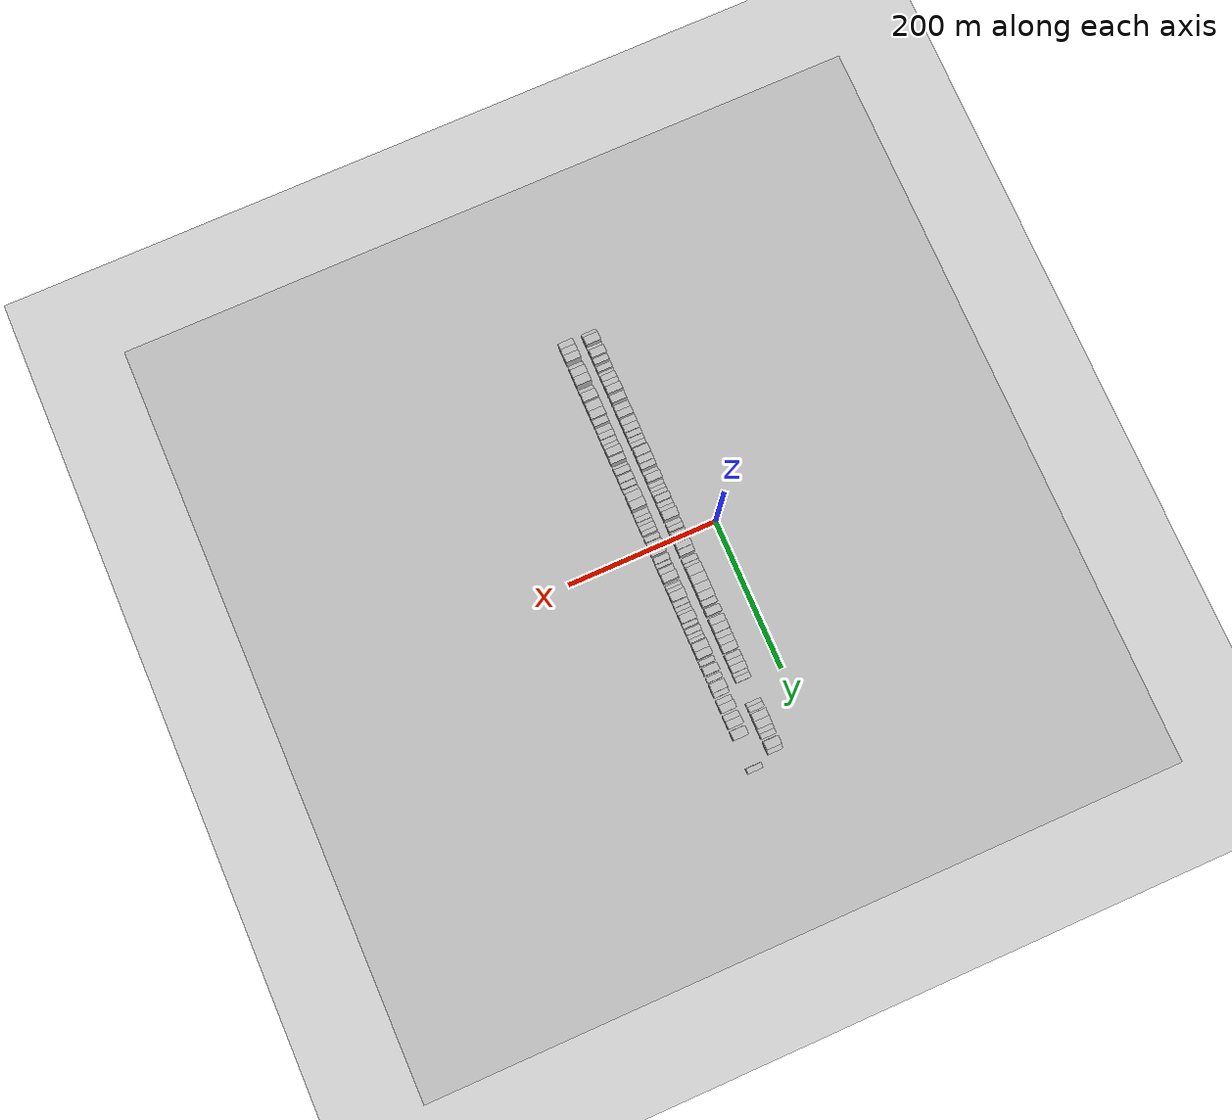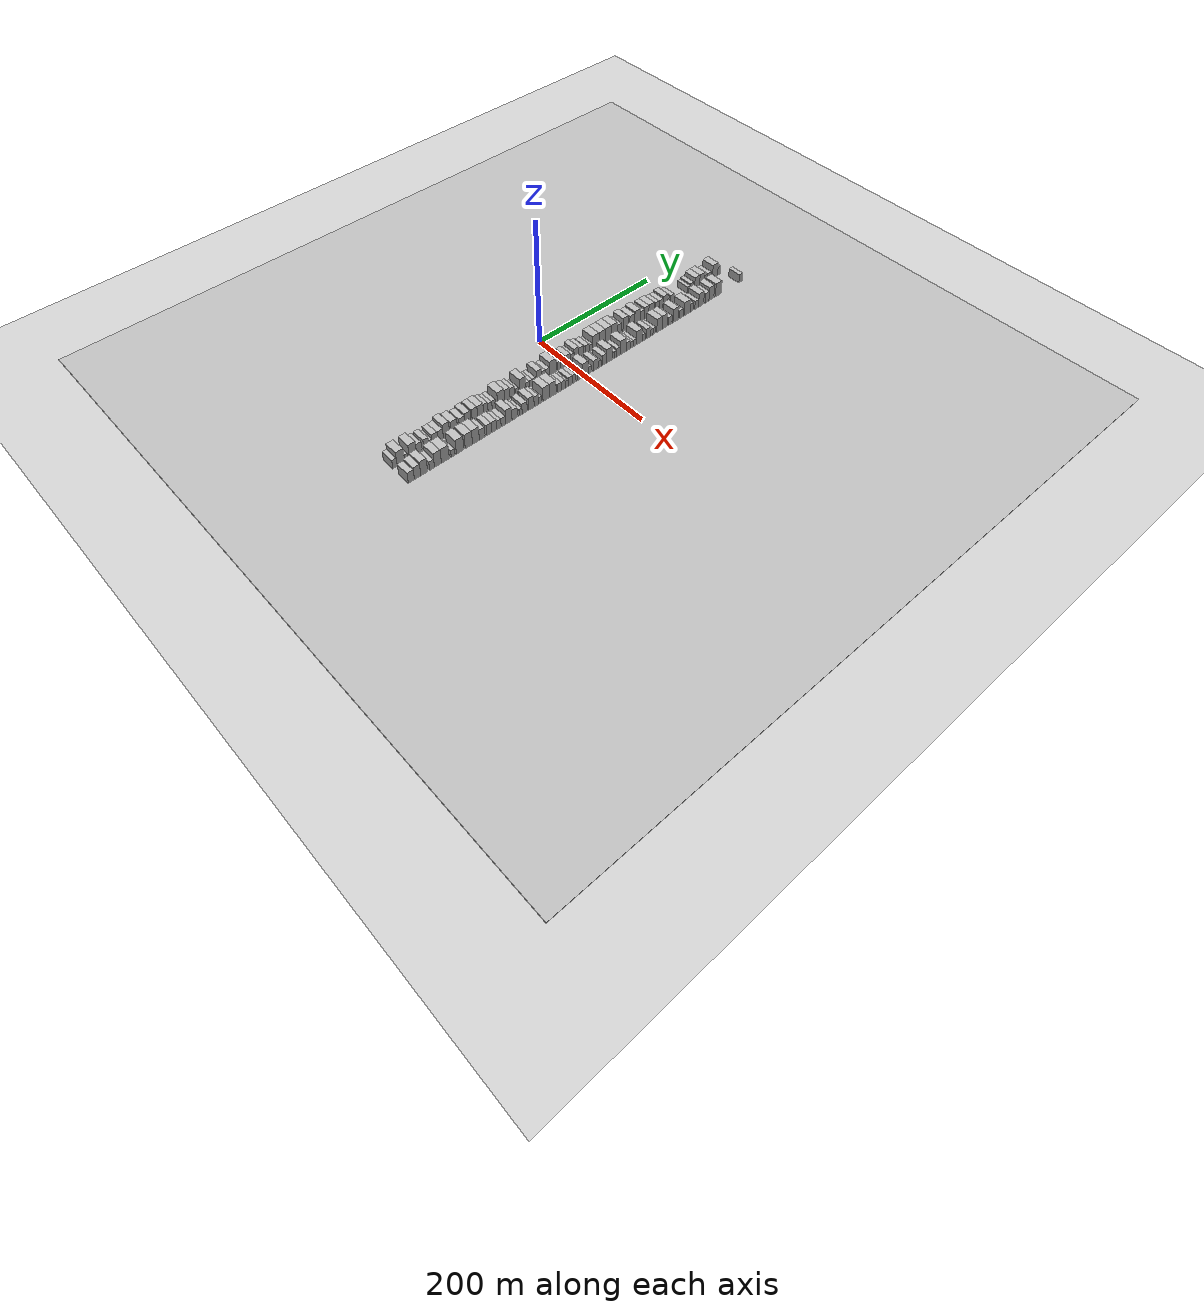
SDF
<?xml version="1.0" encoding="utf-8"?>

<sdf version="1.6">

   <world name="default">

      <gui fullscreen="0">

         <camera name="user_camera">

            <pose>-15 0 4.57585 0 0 0</pose>

            <view_controller>orbit</view_controller>

         </camera>

      </gui>

      <scene>

         <sky>

           <clouds>

             <speed>12</speed>

           </clouds>

         </sky>

         <ambient>0.4 0.4 0.4 1</ambient>

         <background>0.7 0.7 0.7 1</background>

         <shadows>1</shadows>

      </scene>

      <gravity>0 0 -9.8066</gravity>

      <magnetic_field>6e-06 2.3e-05 -4.2e-05</magnetic_field>

      <physics default="0" name="default_physics" type="ode">

         <ode>

            <solver>

               <type>quick</type>

               <iters>10</iters>

               <sor>1.0</sor>

               <use_dynamic_moi_rescaling>0</use_dynamic_moi_rescaling>

            </solver>

            <constraints>

               <cfm>0</cfm>

               <erp>0.2</erp>

               <contact_max_correcting_vel>100</contact_max_correcting_vel>

               <contact_surface_layer>0.001</contact_surface_layer>

            </constraints>

         </ode>

         <max_step_size>0.004</max_step_size>

         <real_time_factor>1</real_time_factor>

         <real_time_update_rate>250</real_time_update_rate>

      </physics>

      <light name="sun" type="directional">

         <cast_shadows>1</cast_shadows>

         <pose>0 0 10 0 0 0</pose>

         <diffuse>0.8 0.8 0.8 1</diffuse>

         <specular>0.2 0.2 0.2 1</specular>

         <attenuation>

            <range>1000</range>

            <constant>0.9</constant>

            <linear>0.01</linear>

            <quadratic>0.001</quadratic>

         </attenuation>

         <direction>-0.5 0.1 -0.9</direction>

      </light>

      <include>

         <name>ground_plane_1</name>

         <uri>model://HANNAS_ground_plane</uri>

         <pose>0 0 0  0 0 0</pose>

      </include>

      <include>

         <name>ground_plane_2</name>

         <uri>model://HANNAS_ground_plane</uri>

         <pose>100 0 0  0 0 0</pose>

      </include>

      <model name="building_1">

         <static>1</static>

         <pose frame="">50.0000 -280.7285 0 0.000000 0.000000 0.000000</pose>

         <link name="link">

            <pose frame="">0 0 7.50 0 0 0</pose>

            <collision name="collision">

               <geometry>

                  <box>

                     <size>20.0000 6.5430 15.0000</size>

                  </box>

               </geometry>

               <max_contacts>10</max_contacts>

               <surface>

                  <contact>

                     <ode/>

                  </contact>

                  <bounce/>

                  <friction>

                     <torsional>

                        <ode/>

                     </torsional>

                     <ode/>

                  </friction>

               </surface>

            </collision>

            <visual name="visual">

               <cast_shadows>0</cast_shadows>

               <geometry>

                  <box>

                     <size>20.0000 6.5430 15.0000</size>

                  </box>

               </geometry>

               <material>

                  <script>

                     <uri>model://HANNAS_wall/materials/scripts</uri>

                     <uri>model://HANNAS_wall/materials/textures</uri>

                     <name>vrc/HANNAS_wall</name>

                  </script>

               </material>

            </visual>

            <self_collide>0</self_collide>

            <enable_wind>0</enable_wind>

            <kinematic>0</kinematic>

         </link>

      </model>

      <model name="building_2">

         <static>1</static>

         <pose frame="">50.0000 -271.9288 0 0.000000 0.000000 0.000000</pose>

         <link name="link">

            <pose frame="">0 0 12.00 0 0 0</pose>

            <collision name="collision">

               <geometry>

                  <box>

                     <size>20.0000 11.0564 24.0000</size>

                  </box>

               </geometry>

               <max_contacts>10</max_contacts>

               <surface>

                  <contact>

                     <ode/>

                  </contact>

                  <bounce/>

                  <friction>

                     <torsional>

                        <ode/>

                     </torsional>

                     <ode/>

                  </friction>

               </surface>

            </collision>

            <visual name="visual">

               <cast_shadows>0</cast_shadows>

               <geometry>

                  <box>

                     <size>20.0000 11.0564 24.0000</size>

                  </box>

               </geometry>

               <material>

                  <script>

                     <uri>model://HANNAS_wall/materials/scripts</uri>

                     <uri>model://HANNAS_wall/materials/textures</uri>

                     <name>vrc/HANNAS_wall</name>

                  </script>

               </material>

            </visual>

            <self_collide>0</self_collide>

            <enable_wind>0</enable_wind>

            <kinematic>0</kinematic>

         </link>

      </model>

      <model name="building_3">

         <static>1</static>

         <pose frame="">50.0000 -263.8461 0 0.000000 0.000000 0.000000</pose>

         <link name="link">

            <pose frame="">0 0 6.00 0 0 0</pose>

            <collision name="collision">

               <geometry>

                  <box>

                     <size>20.0000 5.1090 12.0000</size>

                  </box>

               </geometry>

               <max_contacts>10</max_contacts>

               <surface>

                  <contact>

                     <ode/>

                  </contact>

                  <bounce/>

                  <friction>

                     <torsional>

                        <ode/>

                     </torsional>

                     <ode/>

                  </friction>

               </surface>

            </collision>

            <visual name="visual">

               <cast_shadows>0</cast_shadows>

               <geometry>

                  <box>

                     <size>20.0000 5.1090 12.0000</size>

                  </box>

               </geometry>

               <material>

                  <script>

                     <uri>model://HANNAS_wall/materials/scripts</uri>

                     <uri>model://HANNAS_wall/materials/textures</uri>

                     <name>vrc/HANNAS_wall</name>

                  </script>

               </material>

            </visual>

            <self_collide>0</self_collide>

            <enable_wind>0</enable_wind>

            <kinematic>0</kinematic>

         </link>

      </model>

      <model name="building_4">

         <static>1</static>

         <pose frame="">50.0000 -253.8942 0 0.000000 0.000000 0.000000</pose>

         <link name="link">

            <pose frame="">0 0 12.00 0 0 0</pose>

            <collision name="collision">

               <geometry>

                  <box>

                     <size>20.0000 10.7950 24.0000</size>

                  </box>

               </geometry>

               <max_contacts>10</max_contacts>

               <surface>

                  <contact>

                     <ode/>

                  </contact>

                  <bounce/>

                  <friction>

                     <torsional>

                        <ode/>

                     </torsional>

                     <ode/>

                  </friction>

               </surface>

            </collision>

            <visual name="visual">

               <cast_shadows>0</cast_shadows>

               <geometry>

                  <box>

                     <size>20.0000 10.7950 24.0000</size>

                  </box>

               </geometry>

               <material>

                  <script>

                     <uri>model://HANNAS_wall/materials/scripts</uri>

                     <uri>model://HANNAS_wall/materials/textures</uri>

                     <name>vrc/HANNAS_wall</name>

                  </script>

               </material>

            </visual>

            <self_collide>0</self_collide>

            <enable_wind>0</enable_wind>

            <kinematic>0</kinematic>

         </link>

      </model>

      <model name="building_5">

         <static>1</static>

         <pose frame="">50.0000 -244.4497 0 0.000000 0.000000 0.000000</pose>

         <link name="link">

            <pose frame="">0 0 9.00 0 0 0</pose>

            <collision name="collision">

               <geometry>

                  <box>

                     <size>20.0000 8.0939 18.0000</size>

                  </box>

               </geometry>

               <max_contacts>10</max_contacts>

               <surface>

                  <contact>

                     <ode/>

                  </contact>

                  <bounce/>

                  <friction>

                     <torsional>

                        <ode/>

                     </torsional>

                     <ode/>

                  </friction>

               </surface>

            </collision>

            <visual name="visual">

               <cast_shadows>0</cast_shadows>

               <geometry>

                  <box>

                     <size>20.0000 8.0939 18.0000</size>

                  </box>

               </geometry>

               <material>

                  <script>

                     <uri>model://HANNAS_wall/materials/scripts</uri>

                     <uri>model://HANNAS_wall/materials/textures</uri>

                     <name>vrc/HANNAS_wall</name>

                  </script>

               </material>

            </visual>

            <self_collide>0</self_collide>

            <enable_wind>0</enable_wind>

            <kinematic>0</kinematic>

         </link>

      </model>

      <model name="building_6">

         <static>1</static>

         <pose frame="">50.0000 -233.5920 0 0.000000 0.000000 0.000000</pose>

         <link name="link">

            <pose frame="">0 0 9.00 0 0 0</pose>

            <collision name="collision">

               <geometry>

                  <box>

                     <size>20.0000 7.6216 18.0000</size>

                  </box>

               </geometry>

               <max_contacts>10</max_contacts>

               <surface>

                  <contact>

                     <ode/>

                  </contact>

                  <bounce/>

                  <friction>

                     <torsional>

                        <ode/>

                     </torsional>

                     <ode/>

                  </friction>

               </surface>

            </collision>

            <visual name="visual">

               <cast_shadows>0</cast_shadows>

               <geometry>

                  <box>

                     <size>20.0000 7.6216 18.0000</size>

                  </box>

               </geometry>

               <material>

                  <script>

                     <uri>model://HANNAS_wall/materials/scripts</uri>

                     <uri>model://HANNAS_wall/materials/textures</uri>

                     <name>vrc/HANNAS_wall</name>

                  </script>

               </material>

            </visual>

            <self_collide>0</self_collide>

            <enable_wind>0</enable_wind>

            <kinematic>0</kinematic>

         </link>

      </model>

      <model name="building_7">

         <static>1</static>

         <pose frame="">50.0000 -227.0531 0 0.000000 0.000000 0.000000</pose>

         <link name="link">

            <pose frame="">0 0 6.00 0 0 0</pose>

            <collision name="collision">

               <geometry>

                  <box>

                     <size>20.0000 5.4563 12.0000</size>

                  </box>

               </geometry>

               <max_contacts>10</max_contacts>

               <surface>

                  <contact>

                     <ode/>

                  </contact>

                  <bounce/>

                  <friction>

                     <torsional>

                        <ode/>

                     </torsional>

                     <ode/>

                  </friction>

               </surface>

            </collision>

            <visual name="visual">

               <cast_shadows>0</cast_shadows>

               <geometry>

                  <box>

                     <size>20.0000 5.4563 12.0000</size>

                  </box>

               </geometry>

               <material>

                  <script>

                     <uri>model://HANNAS_wall/materials/scripts</uri>

                     <uri>model://HANNAS_wall/materials/textures</uri>

                     <name>vrc/HANNAS_wall</name>

                  </script>

               </material>

            </visual>

            <self_collide>0</self_collide>

            <enable_wind>0</enable_wind>

            <kinematic>0</kinematic>

         </link>

      </model>

      <model name="building_8">

         <static>1</static>

         <pose frame="">50.0000 -220.2378 0 0.000000 0.000000 0.000000</pose>

         <link name="link">

            <pose frame="">0 0 9.00 0 0 0</pose>

            <collision name="collision">

               <geometry>

                  <box>

                     <size>20.0000 8.1742 18.0000</size>

                  </box>

               </geometry>

               <max_contacts>10</max_contacts>

               <surface>

                  <contact>

                     <ode/>

                  </contact>

                  <bounce/>

                  <friction>

                     <torsional>

                        <ode/>

                     </torsional>

                     <ode/>

                  </friction>

               </surface>

            </collision>

            <visual name="visual">

               <cast_shadows>0</cast_shadows>

               <geometry>

                  <box>

                     <size>20.0000 8.1742 18.0000</size>

                  </box>

               </geometry>

               <material>

                  <script>

                     <uri>model://HANNAS_wall/materials/scripts</uri>

                     <uri>model://HANNAS_wall/materials/textures</uri>

                     <name>vrc/HANNAS_wall</name>

                  </script>

               </material>

            </visual>

            <self_collide>0</self_collide>

            <enable_wind>0</enable_wind>

            <kinematic>0</kinematic>

         </link>

      </model>

      <model name="building_9">

         <static>1</static>

         <pose frame="">50.0000 -211.9330 0 0.000000 0.000000 0.000000</pose>

         <link name="link">

            <pose frame="">0 0 9.00 0 0 0</pose>

            <collision name="collision">

               <geometry>

                  <box>

                     <size>20.0000 8.4355 18.0000</size>

                  </box>

               </geometry>

               <max_contacts>10</max_contacts>

               <surface>

                  <contact>

                     <ode/>

                  </contact>

                  <bounce/>

                  <friction>

                     <torsional>

                        <ode/>

                     </torsional>

                     <ode/>

                  </friction>

               </surface>

            </collision>

            <visual name="visual">

               <cast_shadows>0</cast_shadows>

               <geometry>

                  <box>

                     <size>20.0000 8.4355 18.0000</size>

                  </box>

               </geometry>

               <material>

                  <script>

                     <uri>model://HANNAS_wall/materials/scripts</uri>

                     <uri>model://HANNAS_wall/materials/textures</uri>

                     <name>vrc/HANNAS_wall</name>

                  </script>

               </material>

            </visual>

            <self_collide>0</self_collide>

            <enable_wind>0</enable_wind>

            <kinematic>0</kinematic>

         </link>

      </model>

      <model name="building_10">

         <static>1</static>

         <pose frame="">50.0000 -202.7415 0 0.000000 0.000000 0.000000</pose>

         <link name="link">

            <pose frame="">0 0 12.00 0 0 0</pose>

            <collision name="collision">

               <geometry>

                  <box>

                     <size>20.0000 9.9475 24.0000</size>

                  </box>

               </geometry>

               <max_contacts>10</max_contacts>

               <surface>

                  <contact>

                     <ode/>

                  </contact>

                  <bounce/>

                  <friction>

                     <torsional>

                        <ode/>

                     </torsional>

                     <ode/>

                  </friction>

               </surface>

            </collision>

            <visual name="visual">

               <cast_shadows>0</cast_shadows>

               <geometry>

                  <box>

                     <size>20.0000 9.9475 24.0000</size>

                  </box>

               </geometry>

               <material>

                  <script>

                     <uri>model://HANNAS_wall/materials/scripts</uri>

                     <uri>model://HANNAS_wall/materials/textures</uri>

                     <name>vrc/HANNAS_wall</name>

                  </script>

               </material>

            </visual>

            <self_collide>0</self_collide>

            <enable_wind>0</enable_wind>

            <kinematic>0</kinematic>

         </link>

      </model>

      <model name="building_11">

         <static>1</static>

         <pose frame="">50.0000 -190.6426 0 0.000000 0.000000 0.000000</pose>

         <link name="link">

            <pose frame="">0 0 10.50 0 0 0</pose>

            <collision name="collision">

               <geometry>

                  <box>

                     <size>20.0000 10.2502 21.0000</size>

                  </box>

               </geometry>

               <max_contacts>10</max_contacts>

               <surface>

                  <contact>

                     <ode/>

                  </contact>

                  <bounce/>

                  <friction>

                     <torsional>

                        <ode/>

                     </torsional>

                     <ode/>

                  </friction>

               </surface>

            </collision>

            <visual name="visual">

               <cast_shadows>0</cast_shadows>

               <geometry>

                  <box>

                     <size>20.0000 10.2502 21.0000</size>

                  </box>

               </geometry>

               <material>

                  <script>

                     <uri>model://HANNAS_wall/materials/scripts</uri>

                     <uri>model://HANNAS_wall/materials/textures</uri>

                     <name>vrc/HANNAS_wall</name>

                  </script>

               </material>

            </visual>

            <self_collide>0</self_collide>

            <enable_wind>0</enable_wind>

            <kinematic>0</kinematic>

         </link>

      </model>

      <model name="building_12">

         <static>1</static>

         <pose frame="">50.0000 -178.1155 0 0.000000 0.000000 0.000000</pose>

         <link name="link">

            <pose frame="">0 0 9.00 0 0 0</pose>

            <collision name="collision">

               <geometry>

                  <box>

                     <size>20.0000 8.8040 18.0000</size>

                  </box>

               </geometry>

               <max_contacts>10</max_contacts>

               <surface>

                  <contact>

                     <ode/>

                  </contact>

                  <bounce/>

                  <friction>

                     <torsional>

                        <ode/>

                     </torsional>

                     <ode/>

                  </friction>

               </surface>

            </collision>

            <visual name="visual">

               <cast_shadows>0</cast_shadows>

               <geometry>

                  <box>

                     <size>20.0000 8.8040 18.0000</size>

                  </box>

               </geometry>

               <material>

                  <script>

                     <uri>model://HANNAS_wall/materials/scripts</uri>

                     <uri>model://HANNAS_wall/materials/textures</uri>

                     <name>vrc/HANNAS_wall</name>

                  </script>

               </material>

            </visual>

            <self_collide>0</self_collide>

            <enable_wind>0</enable_wind>

            <kinematic>0</kinematic>

         </link>

      </model>

      <model name="building_13">

         <static>1</static>

         <pose frame="">50.0000 -169.1064 0 0.000000 0.000000 0.000000</pose>

         <link name="link">

            <pose frame="">0 0 10.50 0 0 0</pose>

            <collision name="collision">

               <geometry>

                  <box>

                     <size>20.0000 9.2141 21.0000</size>

                  </box>

               </geometry>

               <max_contacts>10</max_contacts>

               <surface>

                  <contact>

                     <ode/>

                  </contact>

                  <bounce/>

                  <friction>

                     <torsional>

                        <ode/>

                     </torsional>

                     <ode/>

                  </friction>

               </surface>

            </collision>

            <visual name="visual">

               <cast_shadows>0</cast_shadows>

               <geometry>

                  <box>

                     <size>20.0000 9.2141 21.0000</size>

                  </box>

               </geometry>

               <material>

                  <script>

                     <uri>model://HANNAS_wall/materials/scripts</uri>

                     <uri>model://HANNAS_wall/materials/textures</uri>

                     <name>vrc/HANNAS_wall</name>

                  </script>

               </material>

            </visual>

            <self_collide>0</self_collide>

            <enable_wind>0</enable_wind>

            <kinematic>0</kinematic>

         </link>

      </model>

      <model name="building_14">

         <static>1</static>

         <pose frame="">50.0000 -158.1400 0 0.000000 0.000000 0.000000</pose>

         <link name="link">

            <pose frame="">0 0 10.50 0 0 0</pose>

            <collision name="collision">

               <geometry>

                  <box>

                     <size>20.0000 8.7185 21.0000</size>

                  </box>

               </geometry>

               <max_contacts>10</max_contacts>

               <surface>

                  <contact>

                     <ode/>

                  </contact>

                  <bounce/>

                  <friction>

                     <torsional>

                        <ode/>

                     </torsional>

                     <ode/>

                  </friction>

               </surface>

            </collision>

            <visual name="visual">

               <cast_shadows>0</cast_shadows>

               <geometry>

                  <box>

                     <size>20.0000 8.7185 21.0000</size>

                  </box>

               </geometry>

               <material>

                  <script>

                     <uri>model://HANNAS_wall/materials/scripts</uri>

                     <uri>model://HANNAS_wall/materials/textures</uri>

                     <name>vrc/HANNAS_wall</name>

                  </script>

               </material>

            </visual>

            <self_collide>0</self_collide>

            <enable_wind>0</enable_wind>

            <kinematic>0</kinematic>

         </link>

      </model>

      <model name="building_15">

         <static>1</static>

         <pose frame="">50.0000 -149.0470 0 0.000000 0.000000 0.000000</pose>

         <link name="link">

            <pose frame="">0 0 10.50 0 0 0</pose>

            <collision name="collision">

               <geometry>

                  <box>

                     <size>20.0000 9.4675 21.0000</size>

                  </box>

               </geometry>

               <max_contacts>10</max_contacts>

               <surface>

                  <contact>

                     <ode/>

                  </contact>

                  <bounce/>

                  <friction>

                     <torsional>

                        <ode/>

                     </torsional>

                     <ode/>

                  </friction>

               </surface>

            </collision>

            <visual name="visual">

               <cast_shadows>0</cast_shadows>

               <geometry>

                  <box>

                     <size>20.0000 9.4675 21.0000</size>

                  </box>

               </geometry>

               <material>

                  <script>

                     <uri>model://HANNAS_wall/materials/scripts</uri>

                     <uri>model://HANNAS_wall/materials/textures</uri>

                     <name>vrc/HANNAS_wall</name>

                  </script>

               </material>

            </visual>

            <self_collide>0</self_collide>

            <enable_wind>0</enable_wind>

            <kinematic>0</kinematic>

         </link>

      </model>

      <model name="building_16">

         <static>1</static>

         <pose frame="">50.0000 -140.7030 0 0.000000 0.000000 0.000000</pose>

         <link name="link">

            <pose frame="">0 0 9.00 0 0 0</pose>

            <collision name="collision">

               <geometry>

                  <box>

                     <size>20.0000 7.2206 18.0000</size>

                  </box>

               </geometry>

               <max_contacts>10</max_contacts>

               <surface>

                  <contact>

                     <ode/>

                  </contact>

                  <bounce/>

                  <friction>

                     <torsional>

                        <ode/>

                     </torsional>

                     <ode/>

                  </friction>

               </surface>

            </collision>

            <visual name="visual">

               <cast_shadows>0</cast_shadows>

               <geometry>

                  <box>

                     <size>20.0000 7.2206 18.0000</size>

                  </box>

               </geometry>

               <material>

                  <script>

                     <uri>model://HANNAS_wall/materials/scripts</uri>

                     <uri>model://HANNAS_wall/materials/textures</uri>

                     <name>vrc/HANNAS_wall</name>

                  </script>

               </material>

            </visual>

            <self_collide>0</self_collide>

            <enable_wind>0</enable_wind>

            <kinematic>0</kinematic>

         </link>

      </model>

      <model name="building_17">

         <static>1</static>

         <pose frame="">50.0000 -133.7853 0 0.000000 0.000000 0.000000</pose>

         <link name="link">

            <pose frame="">0 0 7.50 0 0 0</pose>

            <collision name="collision">

               <geometry>

                  <box>

                     <size>20.0000 6.6148 15.0000</size>

                  </box>

               </geometry>

               <max_contacts>10</max_contacts>

               <surface>

                  <contact>

                     <ode/>

                  </contact>

                  <bounce/>

                  <friction>

                     <torsional>

                        <ode/>

                     </torsional>

                     <ode/>

                  </friction>

               </surface>

            </collision>

            <visual name="visual">

               <cast_shadows>0</cast_shadows>

               <geometry>

                  <box>

                     <size>20.0000 6.6148 15.0000</size>

                  </box>

               </geometry>

               <material>

                  <script>

                     <uri>model://HANNAS_wall/materials/scripts</uri>

                     <uri>model://HANNAS_wall/materials/textures</uri>

                     <name>vrc/HANNAS_wall</name>

                  </script>

               </material>

            </visual>

            <self_collide>0</self_collide>

            <enable_wind>0</enable_wind>

            <kinematic>0</kinematic>

         </link>

      </model>

      <model name="building_18">

         <static>1</static>

         <pose frame="">50.0000 -127.4758 0 0.000000 0.000000 0.000000</pose>

         <link name="link">

            <pose frame="">0 0 7.50 0 0 0</pose>

            <collision name="collision">

               <geometry>

                  <box>

                     <size>20.0000 6.0041 15.0000</size>

                  </box>

               </geometry>

               <max_contacts>10</max_contacts>

               <surface>

                  <contact>

                     <ode/>

                  </contact>

                  <bounce/>

                  <friction>

                     <torsional>

                        <ode/>

                     </torsional>

                     <ode/>

                  </friction>

               </surface>

            </collision>

            <visual name="visual">

               <cast_shadows>0</cast_shadows>

               <geometry>

                  <box>

                     <size>20.0000 6.0041 15.0000</size>

                  </box>

               </geometry>

               <material>

                  <script>

                     <uri>model://HANNAS_wall/materials/scripts</uri>

                     <uri>model://HANNAS_wall/materials/textures</uri>

                     <name>vrc/HANNAS_wall</name>

                  </script>

               </material>

            </visual>

            <self_collide>0</self_collide>

            <enable_wind>0</enable_wind>

            <kinematic>0</kinematic>

         </link>

      </model>

      <model name="building_19">

         <static>1</static>

         <pose frame="">50.0000 -115.7782 0 0.000000 0.000000 0.000000</pose>

         <link name="link">

            <pose frame="">0 0 12.00 0 0 0</pose>

            <collision name="collision">

               <geometry>

                  <box>

                     <size>20.0000 11.3912 24.0000</size>

                  </box>

               </geometry>

               <max_contacts>10</max_contacts>

               <surface>

                  <contact>

                     <ode/>

                  </contact>

                  <bounce/>

                  <friction>

                     <torsional>

                        <ode/>

                     </torsional>

                     <ode/>

                  </friction>

               </surface>

            </collision>

            <visual name="visual">

               <cast_shadows>0</cast_shadows>

               <geometry>

                  <box>

                     <size>20.0000 11.3912 24.0000</size>

                  </box>

               </geometry>

               <material>

                  <script>

                     <uri>model://HANNAS_wall/materials/scripts</uri>

                     <uri>model://HANNAS_wall/materials/textures</uri>

                     <name>vrc/HANNAS_wall</name>

                  </script>

               </material>

            </visual>

            <self_collide>0</self_collide>

            <enable_wind>0</enable_wind>

            <kinematic>0</kinematic>

         </link>

      </model>

      <model name="building_20">

         <static>1</static>

         <pose frame="">50.0000 -105.6370 0 0.000000 0.000000 0.000000</pose>

         <link name="link">

            <pose frame="">0 0 10.50 0 0 0</pose>

            <collision name="collision">

               <geometry>

                  <box>

                     <size>20.0000 8.8911 21.0000</size>

                  </box>

               </geometry>

               <max_contacts>10</max_contacts>

               <surface>

                  <contact>

                     <ode/>

                  </contact>

                  <bounce/>

                  <friction>

                     <torsional>

                        <ode/>

                     </torsional>

                     <ode/>

                  </friction>

               </surface>

            </collision>

            <visual name="visual">

               <cast_shadows>0</cast_shadows>

               <geometry>

                  <box>

                     <size>20.0000 8.8911 21.0000</size>

                  </box>

               </geometry>

               <material>

                  <script>

                     <uri>model://HANNAS_wall/materials/scripts</uri>

                     <uri>model://HANNAS_wall/materials/textures</uri>

                     <name>vrc/HANNAS_wall</name>

                  </script>

               </material>

            </visual>

            <self_collide>0</self_collide>

            <enable_wind>0</enable_wind>

            <kinematic>0</kinematic>

         </link>

      </model>

      <model name="building_21">

         <static>1</static>

         <pose frame="">50.0000 -97.4049 0 0.000000 0.000000 0.000000</pose>

         <link name="link">

            <pose frame="">0 0 9.00 0 0 0</pose>

            <collision name="collision">

               <geometry>

                  <box>

                     <size>20.0000 7.5730 18.0000</size>

                  </box>

               </geometry>

               <max_contacts>10</max_contacts>

               <surface>

                  <contact>

                     <ode/>

                  </contact>

                  <bounce/>

                  <friction>

                     <torsional>

                        <ode/>

                     </torsional>

                     <ode/>

                  </friction>

               </surface>

            </collision>

            <visual name="visual">

               <cast_shadows>0</cast_shadows>

               <geometry>

                  <box>

                     <size>20.0000 7.5730 18.0000</size>

                  </box>

               </geometry>

               <material>

                  <script>

                     <uri>model://HANNAS_wall/materials/scripts</uri>

                     <uri>model://HANNAS_wall/materials/textures</uri>

                     <name>vrc/HANNAS_wall</name>

                  </script>

               </material>

            </visual>

            <self_collide>0</self_collide>

            <enable_wind>0</enable_wind>

            <kinematic>0</kinematic>

         </link>

      </model>

      <model name="building_22">

         <static>1</static>

         <pose frame="">50.0000 -89.0741 0 0.000000 0.000000 0.000000</pose>

         <link name="link">

            <pose frame="">0 0 6.00 0 0 0</pose>

            <collision name="collision">

               <geometry>

                  <box>

                     <size>20.0000 5.0886 12.0000</size>

                  </box>

               </geometry>

               <max_contacts>10</max_contacts>

               <surface>

                  <contact>

                     <ode/>

                  </contact>

                  <bounce/>

                  <friction>

                     <torsional>

                        <ode/>

                     </torsional>

                     <ode/>

                  </friction>

               </surface>

            </collision>

            <visual name="visual">

               <cast_shadows>0</cast_shadows>

               <geometry>

                  <box>

                     <size>20.0000 5.0886 12.0000</size>

                  </box>

               </geometry>

               <material>

                  <script>

                     <uri>model://HANNAS_wall/materials/scripts</uri>

                     <uri>model://HANNAS_wall/materials/textures</uri>

                     <name>vrc/HANNAS_wall</name>

                  </script>

               </material>

            </visual>

            <self_collide>0</self_collide>

            <enable_wind>0</enable_wind>

            <kinematic>0</kinematic>

         </link>

      </model>

      <model name="building_23">

         <static>1</static>

         <pose frame="">50.0000 -79.5198 0 0.000000 0.000000 0.000000</pose>

         <link name="link">

            <pose frame="">0 0 12.00 0 0 0</pose>

            <collision name="collision">

               <geometry>

                  <box>

                     <size>20.0000 10.0201 24.0000</size>

                  </box>

               </geometry>

               <max_contacts>10</max_contacts>

               <surface>

                  <contact>

                     <ode/>

                  </contact>

                  <bounce/>

                  <friction>

                     <torsional>

                        <ode/>

                     </torsional>

                     <ode/>

                  </friction>

               </surface>

            </collision>

            <visual name="visual">

               <cast_shadows>0</cast_shadows>

               <geometry>

                  <box>

                     <size>20.0000 10.0201 24.0000</size>

                  </box>

               </geometry>

               <material>

                  <script>

                     <uri>model://HANNAS_wall/materials/scripts</uri>

                     <uri>model://HANNAS_wall/materials/textures</uri>

                     <name>vrc/HANNAS_wall</name>

                  </script>

               </material>

            </visual>

            <self_collide>0</self_collide>

            <enable_wind>0</enable_wind>

            <kinematic>0</kinematic>

         </link>

      </model>

      <model name="building_24">

         <static>1</static>

         <pose frame="">50.0000 -71.6095 0 0.000000 0.000000 0.000000</pose>

         <link name="link">

            <pose frame="">0 0 6.00 0 0 0</pose>

            <collision name="collision">

               <geometry>

                  <box>

                     <size>20.0000 5.8004 12.0000</size>

                  </box>

               </geometry>

               <max_contacts>10</max_contacts>

               <surface>

                  <contact>

                     <ode/>

                  </contact>

                  <bounce/>

                  <friction>

                     <torsional>

                        <ode/>

                     </torsional>

                     <ode/>

                  </friction>

               </surface>

            </collision>

            <visual name="visual">

               <cast_shadows>0</cast_shadows>

               <geometry>

                  <box>

                     <size>20.0000 5.8004 12.0000</size>

                  </box>

               </geometry>

               <material>

                  <script>

                     <uri>model://HANNAS_wall/materials/scripts</uri>

                     <uri>model://HANNAS_wall/materials/textures</uri>

                     <name>vrc/HANNAS_wall</name>

                  </script>

               </material>

            </visual>

            <self_collide>0</self_collide>

            <enable_wind>0</enable_wind>

            <kinematic>0</kinematic>

         </link>

      </model>

      <model name="building_25">

         <static>1</static>

         <pose frame="">50.0000 -65.9958 0 0.000000 0.000000 0.000000</pose>

         <link name="link">

            <pose frame="">0 0 6.00 0 0 0</pose>

            <collision name="collision">

               <geometry>

                  <box>

                     <size>20.0000 5.4270 12.0000</size>

                  </box>

               </geometry>

               <max_contacts>10</max_contacts>

               <surface>

                  <contact>

                     <ode/>

                  </contact>

                  <bounce/>

                  <friction>

                     <torsional>

                        <ode/>

                     </torsional>

                     <ode/>

                  </friction>

               </surface>

            </collision>

            <visual name="visual">

               <cast_shadows>0</cast_shadows>

               <geometry>

                  <box>

                     <size>20.0000 5.4270 12.0000</size>

                  </box>

               </geometry>

               <material>

                  <script>

                     <uri>model://HANNAS_wall/materials/scripts</uri>

                     <uri>model://HANNAS_wall/materials/textures</uri>

                     <name>vrc/HANNAS_wall</name>

                  </script>

               </material>

            </visual>

            <self_collide>0</self_collide>

            <enable_wind>0</enable_wind>

            <kinematic>0</kinematic>

         </link>

      </model>

      <model name="building_26">

         <static>1</static>

         <pose frame="">50.0000 -60.5416 0 0.000000 0.000000 0.000000</pose>

         <link name="link">

            <pose frame="">0 0 6.00 0 0 0</pose>

            <collision name="collision">

               <geometry>

                  <box>

                     <size>20.0000 5.4814 12.0000</size>

                  </box>

               </geometry>

               <max_contacts>10</max_contacts>

               <surface>

                  <contact>

                     <ode/>

                  </contact>

                  <bounce/>

                  <friction>

                     <torsional>

                        <ode/>

                     </torsional>

                     <ode/>

                  </friction>

               </surface>

            </collision>

            <visual name="visual">

               <cast_shadows>0</cast_shadows>

               <geometry>

                  <box>

                     <size>20.0000 5.4814 12.0000</size>

                  </box>

               </geometry>

               <material>

                  <script>

                     <uri>model://HANNAS_wall/materials/scripts</uri>

                     <uri>model://HANNAS_wall/materials/textures</uri>

                     <name>vrc/HANNAS_wall</name>

                  </script>

               </material>

            </visual>

            <self_collide>0</self_collide>

            <enable_wind>0</enable_wind>

            <kinematic>0</kinematic>

         </link>

      </model>

      <model name="building_27">

         <static>1</static>

         <pose frame="">50.0000 -51.5552 0 0.000000 0.000000 0.000000</pose>

         <link name="link">

            <pose frame="">0 0 10.50 0 0 0</pose>

            <collision name="collision">

               <geometry>

                  <box>

                     <size>20.0000 8.4914 21.0000</size>

                  </box>

               </geometry>

               <max_contacts>10</max_contacts>

               <surface>

                  <contact>

                     <ode/>

                  </contact>

                  <bounce/>

                  <friction>

                     <torsional>

                        <ode/>

                     </torsional>

                     <ode/>

                  </friction>

               </surface>

            </collision>

            <visual name="visual">

               <cast_shadows>0</cast_shadows>

               <geometry>

                  <box>

                     <size>20.0000 8.4914 21.0000</size>

                  </box>

               </geometry>

               <material>

                  <script>

                     <uri>model://HANNAS_wall/materials/scripts</uri>

                     <uri>model://HANNAS_wall/materials/textures</uri>

                     <name>vrc/HANNAS_wall</name>

                  </script>

               </material>

            </visual>

            <self_collide>0</self_collide>

            <enable_wind>0</enable_wind>

            <kinematic>0</kinematic>

         </link>

      </model>

      <model name="building_28">

         <static>1</static>

         <pose frame="">50.0000 -44.2493 0 0.000000 0.000000 0.000000</pose>

         <link name="link">

            <pose frame="">0 0 7.50 0 0 0</pose>

            <collision name="collision">

               <geometry>

                  <box>

                     <size>20.0000 6.1206 15.0000</size>

                  </box>

               </geometry>

               <max_contacts>10</max_contacts>

               <surface>

                  <contact>

                     <ode/>

                  </contact>

                  <bounce/>

                  <friction>

                     <torsional>

                        <ode/>

                     </torsional>

                     <ode/>

                  </friction>

               </surface>

            </collision>

            <visual name="visual">

               <cast_shadows>0</cast_shadows>

               <geometry>

                  <box>

                     <size>20.0000 6.1206 15.0000</size>

                  </box>

               </geometry>

               <material>

                  <script>

                     <uri>model://HANNAS_wall/materials/scripts</uri>

                     <uri>model://HANNAS_wall/materials/textures</uri>

                     <name>vrc/HANNAS_wall</name>

                  </script>

               </material>

            </visual>

            <self_collide>0</self_collide>

            <enable_wind>0</enable_wind>

            <kinematic>0</kinematic>

         </link>

      </model>

      <model name="building_29">

         <static>1</static>

         <pose frame="">50.0000 -37.8376 0 0.000000 0.000000 0.000000</pose>

         <link name="link">

            <pose frame="">0 0 7.50 0 0 0</pose>

            <collision name="collision">

               <geometry>

                  <box>

                     <size>20.0000 6.7027 15.0000</size>

                  </box>

               </geometry>

               <max_contacts>10</max_contacts>

               <surface>

                  <contact>

                     <ode/>

                  </contact>

                  <bounce/>

                  <friction>

                     <torsional>

                        <ode/>

                     </torsional>

                     <ode/>

                  </friction>

               </surface>

            </collision>

            <visual name="visual">

               <cast_shadows>0</cast_shadows>

               <geometry>

                  <box>

                     <size>20.0000 6.7027 15.0000</size>

                  </box>

               </geometry>

               <material>

                  <script>

                     <uri>model://HANNAS_wall/materials/scripts</uri>

                     <uri>model://HANNAS_wall/materials/textures</uri>

                     <name>vrc/HANNAS_wall</name>

                  </script>

               </material>

            </visual>

            <self_collide>0</self_collide>

            <enable_wind>0</enable_wind>

            <kinematic>0</kinematic>

         </link>

      </model>

      <model name="building_30">

         <static>1</static>

         <pose frame="">50.0000 -28.7276 0 0.000000 0.000000 0.000000</pose>

         <link name="link">

            <pose frame="">0 0 12.00 0 0 0</pose>

            <collision name="collision">

               <geometry>

                  <box>

                     <size>20.0000 11.5173 24.0000</size>

                  </box>

               </geometry>

               <max_contacts>10</max_contacts>

               <surface>

                  <contact>

                     <ode/>

                  </contact>

                  <bounce/>

                  <friction>

                     <torsional>

                        <ode/>

                     </torsional>

                     <ode/>

                  </friction>

               </surface>

            </collision>

            <visual name="visual">

               <cast_shadows>0</cast_shadows>

               <geometry>

                  <box>

                     <size>20.0000 11.5173 24.0000</size>

                  </box>

               </geometry>

               <material>

                  <script>

                     <uri>model://HANNAS_wall/materials/scripts</uri>

                     <uri>model://HANNAS_wall/materials/textures</uri>

                     <name>vrc/HANNAS_wall</name>

                  </script>

               </material>

            </visual>

            <self_collide>0</self_collide>

            <enable_wind>0</enable_wind>

            <kinematic>0</kinematic>

         </link>

      </model>

      <model name="building_31">

         <static>1</static>

         <pose frame="">50.0000 -17.8754 0 0.000000 0.000000 0.000000</pose>

         <link name="link">

            <pose frame="">0 0 7.50 0 0 0</pose>

            <collision name="collision">

               <geometry>

                  <box>

                     <size>20.0000 6.1872 15.0000</size>

                  </box>

               </geometry>

               <max_contacts>10</max_contacts>

               <surface>

                  <contact>

                     <ode/>

                  </contact>

                  <bounce/>

                  <friction>

                     <torsional>

                        <ode/>

                     </torsional>

                     <ode/>

                  </friction>

               </surface>

            </collision>

            <visual name="visual">

               <cast_shadows>0</cast_shadows>

               <geometry>

                  <box>

                     <size>20.0000 6.1872 15.0000</size>

                  </box>

               </geometry>

               <material>

                  <script>

                     <uri>model://HANNAS_wall/materials/scripts</uri>

                     <uri>model://HANNAS_wall/materials/textures</uri>

                     <name>vrc/HANNAS_wall</name>

                  </script>

               </material>

            </visual>

            <self_collide>0</self_collide>

            <enable_wind>0</enable_wind>

            <kinematic>0</kinematic>

         </link>

      </model>

      <model name="building_32">

         <static>1</static>

         <pose frame="">50.0000 -11.5547 0 0.000000 0.000000 0.000000</pose>

         <link name="link">

            <pose frame="">0 0 7.50 0 0 0</pose>

            <collision name="collision">

               <geometry>

                  <box>

                     <size>20.0000 6.4543 15.0000</size>

                  </box>

               </geometry>

               <max_contacts>10</max_contacts>

               <surface>

                  <contact>

                     <ode/>

                  </contact>

                  <bounce/>

                  <friction>

                     <torsional>

                        <ode/>

                     </torsional>

                     <ode/>

                  </friction>

               </surface>

            </collision>

            <visual name="visual">

               <cast_shadows>0</cast_shadows>

               <geometry>

                  <box>

                     <size>20.0000 6.4543 15.0000</size>

                  </box>

               </geometry>

               <material>

                  <script>

                     <uri>model://HANNAS_wall/materials/scripts</uri>

                     <uri>model://HANNAS_wall/materials/textures</uri>

                     <name>vrc/HANNAS_wall</name>

                  </script>

               </material>

            </visual>

            <self_collide>0</self_collide>

            <enable_wind>0</enable_wind>

            <kinematic>0</kinematic>

         </link>

      </model>

      <model name="building_33">

         <static>1</static>

         <pose frame="">50.0000 -2.1452 0 0.000000 0.000000 0.000000</pose>

         <link name="link">

            <pose frame="">0 0 9.00 0 0 0</pose>

            <collision name="collision">

               <geometry>

                  <box>

                     <size>20.0000 8.3647 18.0000</size>

                  </box>

               </geometry>

               <max_contacts>10</max_contacts>

               <surface>

                  <contact>

                     <ode/>

                  </contact>

                  <bounce/>

                  <friction>

                     <torsional>

                        <ode/>

                     </torsional>

                     <ode/>

                  </friction>

               </surface>

            </collision>

            <visual name="visual">

               <cast_shadows>0</cast_shadows>

               <geometry>

                  <box>

                     <size>20.0000 8.3647 18.0000</size>

                  </box>

               </geometry>

               <material>

                  <script>

                     <uri>model://HANNAS_wall/materials/scripts</uri>

                     <uri>model://HANNAS_wall/materials/textures</uri>

                     <name>vrc/HANNAS_wall</name>

                  </script>

               </material>

            </visual>

            <self_collide>0</self_collide>

            <enable_wind>0</enable_wind>

            <kinematic>0</kinematic>

         </link>

      </model>

      <model name="building_34">

         <static>1</static>

         <pose frame="">50.0000 5.1659 0 0.000000 0.000000 0.000000</pose>

         <link name="link">

            <pose frame="">0 0 7.50 0 0 0</pose>

            <collision name="collision">

               <geometry>

                  <box>

                     <size>20.0000 6.2576 15.0000</size>

                  </box>

               </geometry>

               <max_contacts>10</max_contacts>

               <surface>

                  <contact>

                     <ode/>

                  </contact>

                  <bounce/>

                  <friction>

                     <torsional>

                        <ode/>

                     </torsional>

                     <ode/>

                  </friction>

               </surface>

            </collision>

            <visual name="visual">

               <cast_shadows>0</cast_shadows>

               <geometry>

                  <box>

                     <size>20.0000 6.2576 15.0000</size>

                  </box>

               </geometry>

               <material>

                  <script>

                     <uri>model://HANNAS_wall/materials/scripts</uri>

                     <uri>model://HANNAS_wall/materials/textures</uri>

                     <name>vrc/HANNAS_wall</name>

                  </script>

               </material>

            </visual>

            <self_collide>0</self_collide>

            <enable_wind>0</enable_wind>

            <kinematic>0</kinematic>

         </link>

      </model>

      <model name="building_35">

         <static>1</static>

         <pose frame="">50.0000 12.5445 0 0.000000 0.000000 0.000000</pose>

         <link name="link">

            <pose frame="">0 0 10.50 0 0 0</pose>

            <collision name="collision">

               <geometry>

                  <box>

                     <size>20.0000 8.4996 21.0000</size>

                  </box>

               </geometry>

               <max_contacts>10</max_contacts>

               <surface>

                  <contact>

                     <ode/>

                  </contact>

                  <bounce/>

                  <friction>

                     <torsional>

                        <ode/>

                     </torsional>

                     <ode/>

                  </friction>

               </surface>

            </collision>

            <visual name="visual">

               <cast_shadows>0</cast_shadows>

               <geometry>

                  <box>

                     <size>20.0000 8.4996 21.0000</size>

                  </box>

               </geometry>

               <material>

                  <script>

                     <uri>model://HANNAS_wall/materials/scripts</uri>

                     <uri>model://HANNAS_wall/materials/textures</uri>

                     <name>vrc/HANNAS_wall</name>

                  </script>

               </material>

            </visual>

            <self_collide>0</self_collide>

            <enable_wind>0</enable_wind>

            <kinematic>0</kinematic>

         </link>

      </model>

      <model name="building_36">

         <static>1</static>

         <pose frame="">50.0000 20.9216 0 0.000000 0.000000 0.000000</pose>

         <link name="link">

            <pose frame="">0 0 9.00 0 0 0</pose>

            <collision name="collision">

               <geometry>

                  <box>

                     <size>20.0000 8.2547 18.0000</size>

                  </box>

               </geometry>

               <max_contacts>10</max_contacts>

               <surface>

                  <contact>

                     <ode/>

                  </contact>

                  <bounce/>

                  <friction>

                     <torsional>

                        <ode/>

                     </torsional>

                     <ode/>

                  </friction>

               </surface>

            </collision>

            <visual name="visual">

               <cast_shadows>0</cast_shadows>

               <geometry>

                  <box>

                     <size>20.0000 8.2547 18.0000</size>

                  </box>

               </geometry>

               <material>

                  <script>

                     <uri>model://HANNAS_wall/materials/scripts</uri>

                     <uri>model://HANNAS_wall/materials/textures</uri>

                     <name>vrc/HANNAS_wall</name>

                  </script>

               </material>

            </visual>

            <self_collide>0</self_collide>

            <enable_wind>0</enable_wind>

            <kinematic>0</kinematic>

         </link>

      </model>

      <model name="building_37">

         <static>1</static>

         <pose frame="">50.0000 31.7448 0 0.000000 0.000000 0.000000</pose>

         <link name="link">

            <pose frame="">0 0 7.50 0 0 0</pose>

            <collision name="collision">

               <geometry>

                  <box>

                     <size>20.0000 7.3918 15.0000</size>

                  </box>

               </geometry>

               <max_contacts>10</max_contacts>

               <surface>

                  <contact>

                     <ode/>

                  </contact>

                  <bounce/>

                  <friction>

                     <torsional>

                        <ode/>

                     </torsional>

                     <ode/>

                  </friction>

               </surface>

            </collision>

            <visual name="visual">

               <cast_shadows>0</cast_shadows>

               <geometry>

                  <box>

                     <size>20.0000 7.3918 15.0000</size>

                  </box>

               </geometry>

               <material>

                  <script>

                     <uri>model://HANNAS_wall/materials/scripts</uri>

                     <uri>model://HANNAS_wall/materials/textures</uri>

                     <name>vrc/HANNAS_wall</name>

                  </script>

               </material>

            </visual>

            <self_collide>0</self_collide>

            <enable_wind>0</enable_wind>

            <kinematic>0</kinematic>

         </link>

      </model>

      <model name="building_38">

         <static>1</static>

         <pose frame="">50.0000 38.3287 0 0.000000 0.000000 0.000000</pose>

         <link name="link">

            <pose frame="">0 0 6.00 0 0 0</pose>

            <collision name="collision">

               <geometry>

                  <box>

                     <size>20.0000 5.7759 12.0000</size>

                  </box>

               </geometry>

               <max_contacts>10</max_contacts>

               <surface>

                  <contact>

                     <ode/>

                  </contact>

                  <bounce/>

                  <friction>

                     <torsional>

                        <ode/>

                     </torsional>

                     <ode/>

                  </friction>

               </surface>

            </collision>

            <visual name="visual">

               <cast_shadows>0</cast_shadows>

               <geometry>

                  <box>

                     <size>20.0000 5.7759 12.0000</size>

                  </box>

               </geometry>

               <material>

                  <script>

                     <uri>model://HANNAS_wall/materials/scripts</uri>

                     <uri>model://HANNAS_wall/materials/textures</uri>

                     <name>vrc/HANNAS_wall</name>

                  </script>

               </material>

            </visual>

            <self_collide>0</self_collide>

            <enable_wind>0</enable_wind>

            <kinematic>0</kinematic>

         </link>

      </model>

      <model name="building_39">

         <static>1</static>

         <pose frame="">50.0000 47.1344 0 0.000000 0.000000 0.000000</pose>

         <link name="link">

            <pose frame="">0 0 12.00 0 0 0</pose>

            <collision name="collision">

               <geometry>

                  <box>

                     <size>20.0000 11.8356 24.0000</size>

                  </box>

               </geometry>

               <max_contacts>10</max_contacts>

               <surface>

                  <contact>

                     <ode/>

                  </contact>

                  <bounce/>

                  <friction>

                     <torsional>

                        <ode/>

                     </torsional>

                     <ode/>

                  </friction>

               </surface>

            </collision>

            <visual name="visual">

               <cast_shadows>0</cast_shadows>

               <geometry>

                  <box>

                     <size>20.0000 11.8356 24.0000</size>

                  </box>

               </geometry>

               <material>

                  <script>

                     <uri>model://HANNAS_wall/materials/scripts</uri>

                     <uri>model://HANNAS_wall/materials/textures</uri>

                     <name>vrc/HANNAS_wall</name>

                  </script>

               </material>

            </visual>

            <self_collide>0</self_collide>

            <enable_wind>0</enable_wind>

            <kinematic>0</kinematic>

         </link>

      </model>

      <model name="building_40">

         <static>1</static>

         <pose frame="">50.0000 58.9942 0 0.000000 0.000000 0.000000</pose>

         <link name="link">

            <pose frame="">0 0 12.00 0 0 0</pose>

            <collision name="collision">

               <geometry>

                  <box>

                     <size>20.0000 11.8840 24.0000</size>

                  </box>

               </geometry>

               <max_contacts>10</max_contacts>

               <surface>

                  <contact>

                     <ode/>

                  </contact>

                  <bounce/>

                  <friction>

                     <torsional>

                        <ode/>

                     </torsional>

                     <ode/>

                  </friction>

               </surface>

            </collision>

            <visual name="visual">

               <cast_shadows>0</cast_shadows>

               <geometry>

                  <box>

                     <size>20.0000 11.8840 24.0000</size>

                  </box>

               </geometry>

               <material>

                  <script>

                     <uri>model://HANNAS_wall/materials/scripts</uri>

                     <uri>model://HANNAS_wall/materials/textures</uri>

                     <name>vrc/HANNAS_wall</name>

                  </script>

               </material>

            </visual>

            <self_collide>0</self_collide>

            <enable_wind>0</enable_wind>

            <kinematic>0</kinematic>

         </link>

      </model>

      <model name="building_41">

         <static>1</static>

         <pose frame="">50.0000 70.3936 0 0.000000 0.000000 0.000000</pose>

         <link name="link">

            <pose frame="">0 0 12.00 0 0 0</pose>

            <collision name="collision">

               <geometry>

                  <box>

                     <size>20.0000 10.9147 24.0000</size>

                  </box>

               </geometry>

               <max_contacts>10</max_contacts>

               <surface>

                  <contact>

                     <ode/>

                  </contact>

                  <bounce/>

                  <friction>

                     <torsional>

                        <ode/>

                     </torsional>

                     <ode/>

                  </friction>

               </surface>

            </collision>

            <visual name="visual">

               <cast_shadows>0</cast_shadows>

               <geometry>

                  <box>

                     <size>20.0000 10.9147 24.0000</size>

                  </box>

               </geometry>

               <material>

                  <script>

                     <uri>model://HANNAS_wall/materials/scripts</uri>

                     <uri>model://HANNAS_wall/materials/textures</uri>

                     <name>vrc/HANNAS_wall</name>

                  </script>

               </material>

            </visual>

            <self_collide>0</self_collide>

            <enable_wind>0</enable_wind>

            <kinematic>0</kinematic>

         </link>

      </model>

      <model name="building_42">

         <static>1</static>

         <pose frame="">50.0000 81.1011 0 0.000000 0.000000 0.000000</pose>

         <link name="link">

            <pose frame="">0 0 12.00 0 0 0</pose>

            <collision name="collision">

               <geometry>

                  <box>

                     <size>20.0000 10.5003 24.0000</size>

                  </box>

               </geometry>

               <max_contacts>10</max_contacts>

               <surface>

                  <contact>

                     <ode/>

                  </contact>

                  <bounce/>

                  <friction>

                     <torsional>

                        <ode/>

                     </torsional>

                     <ode/>

                  </friction>

               </surface>

            </collision>

            <visual name="visual">

               <cast_shadows>0</cast_shadows>

               <geometry>

                  <box>

                     <size>20.0000 10.5003 24.0000</size>

                  </box>

               </geometry>

               <material>

                  <script>

                     <uri>model://HANNAS_wall/materials/scripts</uri>

                     <uri>model://HANNAS_wall/materials/textures</uri>

                     <name>vrc/HANNAS_wall</name>

                  </script>

               </material>

            </visual>

            <self_collide>0</self_collide>

            <enable_wind>0</enable_wind>

            <kinematic>0</kinematic>

         </link>

      </model>

      <model name="building_43">

         <static>1</static>

         <pose frame="">50.0000 90.2170 0 0.000000 0.000000 0.000000</pose>

         <link name="link">

            <pose frame="">0 0 9.00 0 0 0</pose>

            <collision name="collision">

               <geometry>

                  <box>

                     <size>20.0000 7.7314 18.0000</size>

                  </box>

               </geometry>

               <max_contacts>10</max_contacts>

               <surface>

                  <contact>

                     <ode/>

                  </contact>

                  <bounce/>

                  <friction>

                     <torsional>

                        <ode/>

                     </torsional>

                     <ode/>

                  </friction>

               </surface>

            </collision>

            <visual name="visual">

               <cast_shadows>0</cast_shadows>

               <geometry>

                  <box>

                     <size>20.0000 7.7314 18.0000</size>

                  </box>

               </geometry>

               <material>

                  <script>

                     <uri>model://HANNAS_wall/materials/scripts</uri>

                     <uri>model://HANNAS_wall/materials/textures</uri>

                     <name>vrc/HANNAS_wall</name>

                  </script>

               </material>

            </visual>

            <self_collide>0</self_collide>

            <enable_wind>0</enable_wind>

            <kinematic>0</kinematic>

         </link>

      </model>

      <model name="building_44">

         <static>1</static>

         <pose frame="">50.0000 101.9413 0 0.000000 0.000000 0.000000</pose>

         <link name="link">

            <pose frame="">0 0 12.00 0 0 0</pose>

            <collision name="collision">

               <geometry>

                  <box>

                     <size>20.0000 9.7173 24.0000</size>

                  </box>

               </geometry>

               <max_contacts>10</max_contacts>

               <surface>

                  <contact>

                     <ode/>

                  </contact>

                  <bounce/>

                  <friction>

                     <torsional>

                        <ode/>

                     </torsional>

                     <ode/>

                  </friction>

               </surface>

            </collision>

            <visual name="visual">

               <cast_shadows>0</cast_shadows>

               <geometry>

                  <box>

                     <size>20.0000 9.7173 24.0000</size>

                  </box>

               </geometry>

               <material>

                  <script>

                     <uri>model://HANNAS_wall/materials/scripts</uri>

                     <uri>model://HANNAS_wall/materials/textures</uri>

                     <name>vrc/HANNAS_wall</name>

                  </script>

               </material>

            </visual>

            <self_collide>0</self_collide>

            <enable_wind>0</enable_wind>

            <kinematic>0</kinematic>

         </link>

      </model>

      <model name="building_45">

         <static>1</static>

         <pose frame="">50.0000 114.4521 0 0.000000 0.000000 0.000000</pose>

         <link name="link">

            <pose frame="">0 0 10.50 0 0 0</pose>

            <collision name="collision">

               <geometry>

                  <box>

                     <size>20.0000 9.3042 21.0000</size>

                  </box>

               </geometry>

               <max_contacts>10</max_contacts>

               <surface>

                  <contact>

                     <ode/>

                  </contact>

                  <bounce/>

                  <friction>

                     <torsional>

                        <ode/>

                     </torsional>

                     <ode/>

                  </friction>

               </surface>

            </collision>

            <visual name="visual">

               <cast_shadows>0</cast_shadows>

               <geometry>

                  <box>

                     <size>20.0000 9.3042 21.0000</size>

                  </box>

               </geometry>

               <material>

                  <script>

                     <uri>model://HANNAS_wall/materials/scripts</uri>

                     <uri>model://HANNAS_wall/materials/textures</uri>

                     <name>vrc/HANNAS_wall</name>

                  </script>

               </material>

            </visual>

            <self_collide>0</self_collide>

            <enable_wind>0</enable_wind>

            <kinematic>0</kinematic>

         </link>

      </model>

      <model name="building_46">

         <static>1</static>

         <pose frame="">50.0000 124.3024 0 0.000000 0.000000 0.000000</pose>

         <link name="link">

            <pose frame="">0 0 12.00 0 0 0</pose>

            <collision name="collision">

               <geometry>

                  <box>

                     <size>20.0000 10.3964 24.0000</size>

                  </box>

               </geometry>

               <max_contacts>10</max_contacts>

               <surface>

                  <contact>

                     <ode/>

                  </contact>

                  <bounce/>

                  <friction>

                     <torsional>

                        <ode/>

                     </torsional>

                     <ode/>

                  </friction>

               </surface>

            </collision>

            <visual name="visual">

               <cast_shadows>0</cast_shadows>

               <geometry>

                  <box>

                     <size>20.0000 10.3964 24.0000</size>

                  </box>

               </geometry>

               <material>

                  <script>

                     <uri>model://HANNAS_wall/materials/scripts</uri>

                     <uri>model://HANNAS_wall/materials/textures</uri>

                     <name>vrc/HANNAS_wall</name>

                  </script>

               </material>

            </visual>

            <self_collide>0</self_collide>

            <enable_wind>0</enable_wind>

            <kinematic>0</kinematic>

         </link>

      </model>

      <model name="building_47">

         <static>1</static>

         <pose frame="">50.0000 133.2978 0 0.000000 0.000000 0.000000</pose>

         <link name="link">

            <pose frame="">0 0 9.00 0 0 0</pose>

            <collision name="collision">

               <geometry>

                  <box>

                     <size>20.0000 7.5946 18.0000</size>

                  </box>

               </geometry>

               <max_contacts>10</max_contacts>

               <surface>

                  <contact>

                     <ode/>

                  </contact>

                  <bounce/>

                  <friction>

                     <torsional>

                        <ode/>

                     </torsional>

                     <ode/>

                  </friction>

               </surface>

            </collision>

            <visual name="visual">

               <cast_shadows>0</cast_shadows>

               <geometry>

                  <box>

                     <size>20.0000 7.5946 18.0000</size>

                  </box>

               </geometry>

               <material>

                  <script>

                     <uri>model://HANNAS_wall/materials/scripts</uri>

                     <uri>model://HANNAS_wall/materials/textures</uri>

                     <name>vrc/HANNAS_wall</name>

                  </script>

               </material>

            </visual>

            <self_collide>0</self_collide>

            <enable_wind>0</enable_wind>

            <kinematic>0</kinematic>

         </link>

      </model>

      <model name="building_48">

         <static>1</static>

         <pose frame="">50.0000 141.4103 0 0.000000 0.000000 0.000000</pose>

         <link name="link">

            <pose frame="">0 0 10.50 0 0 0</pose>

            <collision name="collision">

               <geometry>

                  <box>

                     <size>20.0000 8.6304 21.0000</size>

                  </box>

               </geometry>

               <max_contacts>10</max_contacts>

               <surface>

                  <contact>

                     <ode/>

                  </contact>

                  <bounce/>

                  <friction>

                     <torsional>

                        <ode/>

                     </torsional>

                     <ode/>

                  </friction>

               </surface>

            </collision>

            <visual name="visual">

               <cast_shadows>0</cast_shadows>

               <geometry>

                  <box>

                     <size>20.0000 8.6304 21.0000</size>

                  </box>

               </geometry>

               <material>

                  <script>

                     <uri>model://HANNAS_wall/materials/scripts</uri>

                     <uri>model://HANNAS_wall/materials/textures</uri>

                     <name>vrc/HANNAS_wall</name>

                  </script>

               </material>

            </visual>

            <self_collide>0</self_collide>

            <enable_wind>0</enable_wind>

            <kinematic>0</kinematic>

         </link>

      </model>

      <model name="building_49">

         <static>1</static>

         <pose frame="">50.0000 150.9284 0 0.000000 0.000000 0.000000</pose>

         <link name="link">

            <pose frame="">0 0 10.50 0 0 0</pose>

            <collision name="collision">

               <geometry>

                  <box>

                     <size>20.0000 10.4057 21.0000</size>

                  </box>

               </geometry>

               <max_contacts>10</max_contacts>

               <surface>

                  <contact>

                     <ode/>

                  </contact>

                  <bounce/>

                  <friction>

                     <torsional>

                        <ode/>

                     </torsional>

                     <ode/>

                  </friction>

               </surface>

            </collision>

            <visual name="visual">

               <cast_shadows>0</cast_shadows>

               <geometry>

                  <box>

                     <size>20.0000 10.4057 21.0000</size>

                  </box>

               </geometry>

               <material>

                  <script>

                     <uri>model://HANNAS_wall/materials/scripts</uri>

                     <uri>model://HANNAS_wall/materials/textures</uri>

                     <name>vrc/HANNAS_wall</name>

                  </script>

               </material>

            </visual>

            <self_collide>0</self_collide>

            <enable_wind>0</enable_wind>

            <kinematic>0</kinematic>

         </link>

      </model>

      <model name="building_50">

         <static>1</static>

         <pose frame="">50.0000 161.7996 0 0.000000 0.000000 0.000000</pose>

         <link name="link">

            <pose frame="">0 0 9.00 0 0 0</pose>

            <collision name="collision">

               <geometry>

                  <box>

                     <size>20.0000 7.3368 18.0000</size>

                  </box>

               </geometry>

               <max_contacts>10</max_contacts>

               <surface>

                  <contact>

                     <ode/>

                  </contact>

                  <bounce/>

                  <friction>

                     <torsional>

                        <ode/>

                     </torsional>

                     <ode/>

                  </friction>

               </surface>

            </collision>

            <visual name="visual">

               <cast_shadows>0</cast_shadows>

               <geometry>

                  <box>

                     <size>20.0000 7.3368 18.0000</size>

                  </box>

               </geometry>

               <material>

                  <script>

                     <uri>model://HANNAS_wall/materials/scripts</uri>

                     <uri>model://HANNAS_wall/materials/textures</uri>

                     <name>vrc/HANNAS_wall</name>

                  </script>

               </material>

            </visual>

            <self_collide>0</self_collide>

            <enable_wind>0</enable_wind>

            <kinematic>0</kinematic>

         </link>

      </model>

      <model name="building_51">

         <static>1</static>

         <pose frame="">50.0000 169.3375 0 0.000000 0.000000 0.000000</pose>

         <link name="link">

            <pose frame="">0 0 9.00 0 0 0</pose>

            <collision name="collision">

               <geometry>

                  <box>

                     <size>20.0000 7.7389 18.0000</size>

                  </box>

               </geometry>

               <max_contacts>10</max_contacts>

               <surface>

                  <contact>

                     <ode/>

                  </contact>

                  <bounce/>

                  <friction>

                     <torsional>

                        <ode/>

                     </torsional>

                     <ode/>

                  </friction>

               </surface>

            </collision>

            <visual name="visual">

               <cast_shadows>0</cast_shadows>

               <geometry>

                  <box>

                     <size>20.0000 7.7389 18.0000</size>

                  </box>

               </geometry>

               <material>

                  <script>

                     <uri>model://HANNAS_wall/materials/scripts</uri>

                     <uri>model://HANNAS_wall/materials/textures</uri>

                     <name>vrc/HANNAS_wall</name>

                  </script>

               </material>

            </visual>

            <self_collide>0</self_collide>

            <enable_wind>0</enable_wind>

            <kinematic>0</kinematic>

         </link>

      </model>

      <model name="building_52">

         <static>1</static>

         <pose frame="">50.0000 177.9718 0 0.000000 0.000000 0.000000</pose>

         <link name="link">

            <pose frame="">0 0 10.50 0 0 0</pose>

            <collision name="collision">

               <geometry>

                  <box>

                     <size>20.0000 9.5297 21.0000</size>

                  </box>

               </geometry>

               <max_contacts>10</max_contacts>

               <surface>

                  <contact>

                     <ode/>

                  </contact>

                  <bounce/>

                  <friction>

                     <torsional>

                        <ode/>

                     </torsional>

                     <ode/>

                  </friction>

               </surface>

            </collision>

            <visual name="visual">

               <cast_shadows>0</cast_shadows>

               <geometry>

                  <box>

                     <size>20.0000 9.5297 21.0000</size>

                  </box>

               </geometry>

               <material>

                  <script>

                     <uri>model://HANNAS_wall/materials/scripts</uri>

                     <uri>model://HANNAS_wall/materials/textures</uri>

                     <name>vrc/HANNAS_wall</name>

                  </script>

               </material>

            </visual>

            <self_collide>0</self_collide>

            <enable_wind>0</enable_wind>

            <kinematic>0</kinematic>

         </link>

      </model>

      <model name="building_53">

         <static>1</static>

         <pose frame="">50.0000 185.2828 0 0.000000 0.000000 0.000000</pose>

         <link name="link">

            <pose frame="">0 0 6.00 0 0 0</pose>

            <collision name="collision">

               <geometry>

                  <box>

                     <size>20.0000 5.0922 12.0000</size>

                  </box>

               </geometry>

               <max_contacts>10</max_contacts>

               <surface>

                  <contact>

                     <ode/>

                  </contact>

                  <bounce/>

                  <friction>

                     <torsional>

                        <ode/>

                     </torsional>

                     <ode/>

                  </friction>

               </surface>

            </collision>

            <visual name="visual">

               <cast_shadows>0</cast_shadows>

               <geometry>

                  <box>

                     <size>20.0000 5.0922 12.0000</size>

                  </box>

               </geometry>

               <material>

                  <script>

                     <uri>model://HANNAS_wall/materials/scripts</uri>

                     <uri>model://HANNAS_wall/materials/textures</uri>

                     <name>vrc/HANNAS_wall</name>

                  </script>

               </material>

            </visual>

            <self_collide>0</self_collide>

            <enable_wind>0</enable_wind>

            <kinematic>0</kinematic>

         </link>

      </model>

      <model name="building_54">

         <static>1</static>

         <pose frame="">50.0000 191.3628 0 0.000000 0.000000 0.000000</pose>

         <link name="link">

            <pose frame="">0 0 7.50 0 0 0</pose>

            <collision name="collision">

               <geometry>

                  <box>

                     <size>20.0000 7.0677 15.0000</size>

                  </box>

               </geometry>

               <max_contacts>10</max_contacts>

               <surface>

                  <contact>

                     <ode/>

                  </contact>

                  <bounce/>

                  <friction>

                     <torsional>

                        <ode/>

                     </torsional>

                     <ode/>

                  </friction>

               </surface>

            </collision>

            <visual name="visual">

               <cast_shadows>0</cast_shadows>

               <geometry>

                  <box>

                     <size>20.0000 7.0677 15.0000</size>

                  </box>

               </geometry>

               <material>

                  <script>

                     <uri>model://HANNAS_wall/materials/scripts</uri>

                     <uri>model://HANNAS_wall/materials/textures</uri>

                     <name>vrc/HANNAS_wall</name>

                  </script>

               </material>

            </visual>

            <self_collide>0</self_collide>

            <enable_wind>0</enable_wind>

            <kinematic>0</kinematic>

         </link>

      </model>

      <model name="building_55">

         <static>1</static>

         <pose frame="">50.0000 224.5762 0 0.000000 0.000000 0.000000</pose>

         <link name="link">

            <pose frame="">0 0 6.00 0 0 0</pose>

            <collision name="collision">

               <geometry>

                  <box>

                     <size>20.0000 5.1197 12.0000</size>

                  </box>

               </geometry>

               <max_contacts>10</max_contacts>

               <surface>

                  <contact>

                     <ode/>

                  </contact>

                  <bounce/>

                  <friction>

                     <torsional>

                        <ode/>

                     </torsional>

                     <ode/>

                  </friction>

               </surface>

            </collision>

            <visual name="visual">

               <cast_shadows>0</cast_shadows>

               <geometry>

                  <box>

                     <size>20.0000 5.1197 12.0000</size>

                  </box>

               </geometry>

               <material>

                  <script>

                     <uri>model://HANNAS_wall/materials/scripts</uri>

                     <uri>model://HANNAS_wall/materials/textures</uri>

                     <name>vrc/HANNAS_wall</name>

                  </script>

               </material>

            </visual>

            <self_collide>0</self_collide>

            <enable_wind>0</enable_wind>

            <kinematic>0</kinematic>

         </link>

      </model>

      <model name="building_56">

         <static>1</static>

         <pose frame="">50.0000 230.5793 0 0.000000 0.000000 0.000000</pose>

         <link name="link">

            <pose frame="">0 0 7.50 0 0 0</pose>

            <collision name="collision">

               <geometry>

                  <box>

                     <size>20.0000 6.8864 15.0000</size>

                  </box>

               </geometry>

               <max_contacts>10</max_contacts>

               <surface>

                  <contact>

                     <ode/>

                  </contact>

                  <bounce/>

                  <friction>

                     <torsional>

                        <ode/>

                     </torsional>

                     <ode/>

                  </friction>

               </surface>

            </collision>

            <visual name="visual">

               <cast_shadows>0</cast_shadows>

               <geometry>

                  <box>

                     <size>20.0000 6.8864 15.0000</size>

                  </box>

               </geometry>

               <material>

                  <script>

                     <uri>model://HANNAS_wall/materials/scripts</uri>

                     <uri>model://HANNAS_wall/materials/textures</uri>

                     <name>vrc/HANNAS_wall</name>

                  </script>

               </material>

            </visual>

            <self_collide>0</self_collide>

            <enable_wind>0</enable_wind>

            <kinematic>0</kinematic>

         </link>

      </model>

      <model name="building_57">

         <static>1</static>

         <pose frame="">50.0000 241.0453 0 0.000000 0.000000 0.000000</pose>

         <link name="link">

            <pose frame="">0 0 10.50 0 0 0</pose>

            <collision name="collision">

               <geometry>

                  <box>

                     <size>20.0000 10.0457 21.0000</size>

                  </box>

               </geometry>

               <max_contacts>10</max_contacts>

               <surface>

                  <contact>

                     <ode/>

                  </contact>

                  <bounce/>

                  <friction>

                     <torsional>

                        <ode/>

                     </torsional>

                     <ode/>

                  </friction>

               </surface>

            </collision>

            <visual name="visual">

               <cast_shadows>0</cast_shadows>

               <geometry>

                  <box>

                     <size>20.0000 10.0457 21.0000</size>

                  </box>

               </geometry>

               <material>

                  <script>

                     <uri>model://HANNAS_wall/materials/scripts</uri>

                     <uri>model://HANNAS_wall/materials/textures</uri>

                     <name>vrc/HANNAS_wall</name>

                  </script>

               </material>

            </visual>

            <self_collide>0</self_collide>

            <enable_wind>0</enable_wind>

            <kinematic>0</kinematic>

         </link>

      </model>

      <model name="building_58">

         <static>1</static>

         <pose frame="">50.0000 251.0858 0 0.000000 0.000000 0.000000</pose>

         <link name="link">

            <pose frame="">0 0 10.50 0 0 0</pose>

            <collision name="collision">

               <geometry>

                  <box>

                     <size>20.0000 10.0353 21.0000</size>

                  </box>

               </geometry>

               <max_contacts>10</max_contacts>

               <surface>

                  <contact>

                     <ode/>

                  </contact>

                  <bounce/>

                  <friction>

                     <torsional>

                        <ode/>

                     </torsional>

                     <ode/>

                  </friction>

               </surface>

            </collision>

            <visual name="visual">

               <cast_shadows>0</cast_shadows>

               <geometry>

                  <box>

                     <size>20.0000 10.0353 21.0000</size>

                  </box>

               </geometry>

               <material>

                  <script>

                     <uri>model://HANNAS_wall/materials/scripts</uri>

                     <uri>model://HANNAS_wall/materials/textures</uri>

                     <name>vrc/HANNAS_wall</name>

                  </script>

               </material>

            </visual>

            <self_collide>0</self_collide>

            <enable_wind>0</enable_wind>

            <kinematic>0</kinematic>

         </link>

      </model>

      <model name="building_59">

         <static>1</static>

         <pose frame="">50.0000 259.2685 0 0.000000 0.000000 0.000000</pose>

         <link name="link">

            <pose frame="">0 0 7.50 0 0 0</pose>

            <collision name="collision">

               <geometry>

                  <box>

                     <size>20.0000 6.3301 15.0000</size>

                  </box>

               </geometry>

               <max_contacts>10</max_contacts>

               <surface>

                  <contact>

                     <ode/>

                  </contact>

                  <bounce/>

                  <friction>

                     <torsional>

                        <ode/>

                     </torsional>

                     <ode/>

                  </friction>

               </surface>

            </collision>

            <visual name="visual">

               <cast_shadows>0</cast_shadows>

               <geometry>

                  <box>

                     <size>20.0000 6.3301 15.0000</size>

                  </box>

               </geometry>

               <material>

                  <script>

                     <uri>model://HANNAS_wall/materials/scripts</uri>

                     <uri>model://HANNAS_wall/materials/textures</uri>

                     <name>vrc/HANNAS_wall</name>

                  </script>

               </material>

            </visual>

            <self_collide>0</self_collide>

            <enable_wind>0</enable_wind>

            <kinematic>0</kinematic>

         </link>

      </model>

      <model name="building_60">

         <static>1</static>

         <pose frame="">50.0000 265.8349 0 0.000000 0.000000 0.000000</pose>

         <link name="link">

            <pose frame="">0 0 7.50 0 0 0</pose>

            <collision name="collision">

               <geometry>

                  <box>

                     <size>20.0000 6.8027 15.0000</size>

                  </box>

               </geometry>

               <max_contacts>10</max_contacts>

               <surface>

                  <contact>

                     <ode/>

                  </contact>

                  <bounce/>

                  <friction>

                     <torsional>

                        <ode/>

                     </torsional>

                     <ode/>

                  </friction>

               </surface>

            </collision>

            <visual name="visual">

               <cast_shadows>0</cast_shadows>

               <geometry>

                  <box>

                     <size>20.0000 6.8027 15.0000</size>

                  </box>

               </geometry>

               <material>

                  <script>

                     <uri>model://HANNAS_wall/materials/scripts</uri>

                     <uri>model://HANNAS_wall/materials/textures</uri>

                     <name>vrc/HANNAS_wall</name>

                  </script>

               </material>

            </visual>

            <self_collide>0</self_collide>

            <enable_wind>0</enable_wind>

            <kinematic>0</kinematic>

         </link>

      </model>

      <model name="building_61">

         <static>1</static>

         <pose frame="">50.0000 277.6647 0 0.000000 0.000000 0.000000</pose>

         <link name="link">

            <pose frame="">0 0 12.00 0 0 0</pose>

            <collision name="collision">

               <geometry>

                  <box>

                     <size>20.0000 10.8569 24.0000</size>

                  </box>

               </geometry>

               <max_contacts>10</max_contacts>

               <surface>

                  <contact>

                     <ode/>

                  </contact>

                  <bounce/>

                  <friction>

                     <torsional>

                        <ode/>

                     </torsional>

                     <ode/>

                  </friction>

               </surface>

            </collision>

            <visual name="visual">

               <cast_shadows>0</cast_shadows>

               <geometry>

                  <box>

                     <size>20.0000 10.8569 24.0000</size>

                  </box>

               </geometry>

               <material>

                  <script>

                     <uri>model://HANNAS_wall/materials/scripts</uri>

                     <uri>model://HANNAS_wall/materials/textures</uri>

                     <name>vrc/HANNAS_wall</name>

                  </script>

               </material>

            </visual>

            <self_collide>0</self_collide>

            <enable_wind>0</enable_wind>

            <kinematic>0</kinematic>

         </link>

      </model>

      <model name="building_62">

         <static>1</static>

         <pose frame="">50.0000 286.1082 0 0.000000 0.000000 0.000000</pose>

         <link name="link">

            <pose frame="">0 0 7.50 0 0 0</pose>

            <collision name="collision">

               <geometry>

                  <box>

                     <size>20.0000 6.0302 15.0000</size>

                  </box>

               </geometry>

               <max_contacts>10</max_contacts>

               <surface>

                  <contact>

                     <ode/>

                  </contact>

                  <bounce/>

                  <friction>

                     <torsional>

                        <ode/>

                     </torsional>

                     <ode/>

                  </friction>

               </surface>

            </collision>

            <visual name="visual">

               <cast_shadows>0</cast_shadows>

               <geometry>

                  <box>

                     <size>20.0000 6.0302 15.0000</size>

                  </box>

               </geometry>

               <material>

                  <script>

                     <uri>model://HANNAS_wall/materials/scripts</uri>

                     <uri>model://HANNAS_wall/materials/textures</uri>

                     <name>vrc/HANNAS_wall</name>

                  </script>

               </material>

            </visual>

            <self_collide>0</self_collide>

            <enable_wind>0</enable_wind>

            <kinematic>0</kinematic>

         </link>

      </model>

      <model name="building_63">

         <static>1</static>

         <pose frame="">82.0000 -279.5156 0 0.000000 0.000000 0.000000</pose>

         <link name="link">

            <pose frame="">0 0 9.00 0 0 0</pose>

            <collision name="collision">

               <geometry>

                  <box>

                     <size>20.0000 8.9687 18.0000</size>

                  </box>

               </geometry>

               <max_contacts>10</max_contacts>

               <surface>

                  <contact>

                     <ode/>

                  </contact>

                  <bounce/>

                  <friction>

                     <torsional>

                        <ode/>

                     </torsional>

                     <ode/>

                  </friction>

               </surface>

            </collision>

            <visual name="visual">

               <cast_shadows>0</cast_shadows>

               <geometry>

                  <box>

                     <size>20.0000 8.9687 18.0000</size>

                  </box>

               </geometry>

               <material>

                  <script>

                     <uri>model://HANNAS_wall/materials/scripts</uri>

                     <uri>model://HANNAS_wall/materials/textures</uri>

                     <name>vrc/HANNAS_wall</name>

                  </script>

               </material>

            </visual>

            <self_collide>0</self_collide>

            <enable_wind>0</enable_wind>

            <kinematic>0</kinematic>

         </link>

      </model>

      <model name="building_64">

         <static>1</static>

         <pose frame="">82.0000 -270.2996 0 0.000000 0.000000 0.000000</pose>

         <link name="link">

            <pose frame="">0 0 10.50 0 0 0</pose>

            <collision name="collision">

               <geometry>

                  <box>

                     <size>20.0000 9.4635 21.0000</size>

                  </box>

               </geometry>

               <max_contacts>10</max_contacts>

               <surface>

                  <contact>

                     <ode/>

                  </contact>

                  <bounce/>

                  <friction>

                     <torsional>

                        <ode/>

                     </torsional>

                     <ode/>

                  </friction>

               </surface>

            </collision>

            <visual name="visual">

               <cast_shadows>0</cast_shadows>

               <geometry>

                  <box>

                     <size>20.0000 9.4635 21.0000</size>

                  </box>

               </geometry>

               <material>

                  <script>

                     <uri>model://HANNAS_wall/materials/scripts</uri>

                     <uri>model://HANNAS_wall/materials/textures</uri>

                     <name>vrc/HANNAS_wall</name>

                  </script>

               </material>

            </visual>

            <self_collide>0</self_collide>

            <enable_wind>0</enable_wind>

            <kinematic>0</kinematic>

         </link>

      </model>

      <model name="building_65">

         <static>1</static>

         <pose frame="">82.0000 -260.5115 0 0.000000 0.000000 0.000000</pose>

         <link name="link">

            <pose frame="">0 0 12.00 0 0 0</pose>

            <collision name="collision">

               <geometry>

                  <box>

                     <size>20.0000 10.1127 24.0000</size>

                  </box>

               </geometry>

               <max_contacts>10</max_contacts>

               <surface>

                  <contact>

                     <ode/>

                  </contact>

                  <bounce/>

                  <friction>

                     <torsional>

                        <ode/>

                     </torsional>

                     <ode/>

                  </friction>

               </surface>

            </collision>

            <visual name="visual">

               <cast_shadows>0</cast_shadows>

               <geometry>

                  <box>

                     <size>20.0000 10.1127 24.0000</size>

                  </box>

               </geometry>

               <material>

                  <script>

                     <uri>model://HANNAS_wall/materials/scripts</uri>

                     <uri>model://HANNAS_wall/materials/textures</uri>

                     <name>vrc/HANNAS_wall</name>

                  </script>

               </material>

            </visual>

            <self_collide>0</self_collide>

            <enable_wind>0</enable_wind>

            <kinematic>0</kinematic>

         </link>

      </model>

      <model name="building_66">

         <static>1</static>

         <pose frame="">82.0000 -248.8087 0 0.000000 0.000000 0.000000</pose>

         <link name="link">

            <pose frame="">0 0 7.50 0 0 0</pose>

            <collision name="collision">

               <geometry>

                  <box>

                     <size>20.0000 7.2929 15.0000</size>

                  </box>

               </geometry>

               <max_contacts>10</max_contacts>

               <surface>

                  <contact>

                     <ode/>

                  </contact>

                  <bounce/>

                  <friction>

                     <torsional>

                        <ode/>

                     </torsional>

                     <ode/>

                  </friction>

               </surface>

            </collision>

            <visual name="visual">

               <cast_shadows>0</cast_shadows>

               <geometry>

                  <box>

                     <size>20.0000 7.2929 15.0000</size>

                  </box>

               </geometry>

               <material>

                  <script>

                     <uri>model://HANNAS_wall/materials/scripts</uri>

                     <uri>model://HANNAS_wall/materials/textures</uri>

                     <name>vrc/HANNAS_wall</name>

                  </script>

               </material>

            </visual>

            <self_collide>0</self_collide>

            <enable_wind>0</enable_wind>

            <kinematic>0</kinematic>

         </link>

      </model>

      <model name="building_67">

         <static>1</static>

         <pose frame="">82.0000 -239.9047 0 0.000000 0.000000 0.000000</pose>

         <link name="link">

            <pose frame="">0 0 12.00 0 0 0</pose>

            <collision name="collision">

               <geometry>

                  <box>

                     <size>20.0000 10.5150 24.0000</size>

                  </box>

               </geometry>

               <max_contacts>10</max_contacts>

               <surface>

                  <contact>

                     <ode/>

                  </contact>

                  <bounce/>

                  <friction>

                     <torsional>

                        <ode/>

                     </torsional>

                     <ode/>

                  </friction>

               </surface>

            </collision>

            <visual name="visual">

               <cast_shadows>0</cast_shadows>

               <geometry>

                  <box>

                     <size>20.0000 10.5150 24.0000</size>

                  </box>

               </geometry>

               <material>

                  <script>

                     <uri>model://HANNAS_wall/materials/scripts</uri>

                     <uri>model://HANNAS_wall/materials/textures</uri>

                     <name>vrc/HANNAS_wall</name>

                  </script>

               </material>

            </visual>

            <self_collide>0</self_collide>

            <enable_wind>0</enable_wind>

            <kinematic>0</kinematic>

         </link>

      </model>

      <model name="building_68">

         <static>1</static>

         <pose frame="">82.0000 -228.7389 0 0.000000 0.000000 0.000000</pose>

         <link name="link">

            <pose frame="">0 0 12.00 0 0 0</pose>

            <collision name="collision">

               <geometry>

                  <box>

                     <size>20.0000 11.8166 24.0000</size>

                  </box>

               </geometry>

               <max_contacts>10</max_contacts>

               <surface>

                  <contact>

                     <ode/>

                  </contact>

                  <bounce/>

                  <friction>

                     <torsional>

                        <ode/>

                     </torsional>

                     <ode/>

                  </friction>

               </surface>

            </collision>

            <visual name="visual">

               <cast_shadows>0</cast_shadows>

               <geometry>

                  <box>

                     <size>20.0000 11.8166 24.0000</size>

                  </box>

               </geometry>

               <material>

                  <script>

                     <uri>model://HANNAS_wall/materials/scripts</uri>

                     <uri>model://HANNAS_wall/materials/textures</uri>

                     <name>vrc/HANNAS_wall</name>

                  </script>

               </material>

            </visual>

            <self_collide>0</self_collide>

            <enable_wind>0</enable_wind>

            <kinematic>0</kinematic>

         </link>

      </model>

      <model name="building_69">

         <static>1</static>

         <pose frame="">82.0000 -216.9084 0 0.000000 0.000000 0.000000</pose>

         <link name="link">

            <pose frame="">0 0 6.00 0 0 0</pose>

            <collision name="collision">

               <geometry>

                  <box>

                     <size>20.0000 5.8445 12.0000</size>

                  </box>

               </geometry>

               <max_contacts>10</max_contacts>

               <surface>

                  <contact>

                     <ode/>

                  </contact>

                  <bounce/>

                  <friction>

                     <torsional>

                        <ode/>

                     </torsional>

                     <ode/>

                  </friction>

               </surface>

            </collision>

            <visual name="visual">

               <cast_shadows>0</cast_shadows>

               <geometry>

                  <box>

                     <size>20.0000 5.8445 12.0000</size>

                  </box>

               </geometry>

               <material>

                  <script>

                     <uri>model://HANNAS_wall/materials/scripts</uri>

                     <uri>model://HANNAS_wall/materials/textures</uri>

                     <name>vrc/HANNAS_wall</name>

                  </script>

               </material>

            </visual>

            <self_collide>0</self_collide>

            <enable_wind>0</enable_wind>

            <kinematic>0</kinematic>

         </link>

      </model>

      <model name="building_70">

         <static>1</static>

         <pose frame="">82.0000 -206.1798 0 0.000000 0.000000 0.000000</pose>

         <link name="link">

            <pose frame="">0 0 12.00 0 0 0</pose>

            <collision name="collision">

               <geometry>

                  <box>

                     <size>20.0000 11.6127 24.0000</size>

                  </box>

               </geometry>

               <max_contacts>10</max_contacts>

               <surface>

                  <contact>

                     <ode/>

                  </contact>

                  <bounce/>

                  <friction>

                     <torsional>

                        <ode/>

                     </torsional>

                     <ode/>

                  </friction>

               </surface>

            </collision>

            <visual name="visual">

               <cast_shadows>0</cast_shadows>

               <geometry>

                  <box>

                     <size>20.0000 11.6127 24.0000</size>

                  </box>

               </geometry>

               <material>

                  <script>

                     <uri>model://HANNAS_wall/materials/scripts</uri>

                     <uri>model://HANNAS_wall/materials/textures</uri>

                     <name>vrc/HANNAS_wall</name>

                  </script>

               </material>

            </visual>

            <self_collide>0</self_collide>

            <enable_wind>0</enable_wind>

            <kinematic>0</kinematic>

         </link>

      </model>

      <model name="building_71">

         <static>1</static>

         <pose frame="">82.0000 -192.6436 0 0.000000 0.000000 0.000000</pose>

         <link name="link">

            <pose frame="">0 0 12.00 0 0 0</pose>

            <collision name="collision">

               <geometry>

                  <box>

                     <size>20.0000 11.4597 24.0000</size>

                  </box>

               </geometry>

               <max_contacts>10</max_contacts>

               <surface>

                  <contact>

                     <ode/>

                  </contact>

                  <bounce/>

                  <friction>

                     <torsional>

                        <ode/>

                     </torsional>

                     <ode/>

                  </friction>

               </surface>

            </collision>

            <visual name="visual">

               <cast_shadows>0</cast_shadows>

               <geometry>

                  <box>

                     <size>20.0000 11.4597 24.0000</size>

                  </box>

               </geometry>

               <material>

                  <script>

                     <uri>model://HANNAS_wall/materials/scripts</uri>

                     <uri>model://HANNAS_wall/materials/textures</uri>

                     <name>vrc/HANNAS_wall</name>

                  </script>

               </material>

            </visual>

            <self_collide>0</self_collide>

            <enable_wind>0</enable_wind>

            <kinematic>0</kinematic>

         </link>

      </model>

      <model name="building_72">

         <static>1</static>

         <pose frame="">82.0000 -181.5321 0 0.000000 0.000000 0.000000</pose>

         <link name="link">

            <pose frame="">0 0 12.00 0 0 0</pose>

            <collision name="collision">

               <geometry>

                  <box>

                     <size>20.0000 10.7633 24.0000</size>

                  </box>

               </geometry>

               <max_contacts>10</max_contacts>

               <surface>

                  <contact>

                     <ode/>

                  </contact>

                  <bounce/>

                  <friction>

                     <torsional>

                        <ode/>

                     </torsional>

                     <ode/>

                  </friction>

               </surface>

            </collision>

            <visual name="visual">

               <cast_shadows>0</cast_shadows>

               <geometry>

                  <box>

                     <size>20.0000 10.7633 24.0000</size>

                  </box>

               </geometry>

               <material>

                  <script>

                     <uri>model://HANNAS_wall/materials/scripts</uri>

                     <uri>model://HANNAS_wall/materials/textures</uri>

                     <name>vrc/HANNAS_wall</name>

                  </script>

               </material>

            </visual>

            <self_collide>0</self_collide>

            <enable_wind>0</enable_wind>

            <kinematic>0</kinematic>

         </link>

      </model>

      <model name="building_73">

         <static>1</static>

         <pose frame="">82.0000 -171.7453 0 0.000000 0.000000 0.000000</pose>

         <link name="link">

            <pose frame="">0 0 9.00 0 0 0</pose>

            <collision name="collision">

               <geometry>

                  <box>

                     <size>20.0000 8.8104 18.0000</size>

                  </box>

               </geometry>

               <max_contacts>10</max_contacts>

               <surface>

                  <contact>

                     <ode/>

                  </contact>

                  <bounce/>

                  <friction>

                     <torsional>

                        <ode/>

                     </torsional>

                     <ode/>

                  </friction>

               </surface>

            </collision>

            <visual name="visual">

               <cast_shadows>0</cast_shadows>

               <geometry>

                  <box>

                     <size>20.0000 8.8104 18.0000</size>

                  </box>

               </geometry>

               <material>

                  <script>

                     <uri>model://HANNAS_wall/materials/scripts</uri>

                     <uri>model://HANNAS_wall/materials/textures</uri>

                     <name>vrc/HANNAS_wall</name>

                  </script>

               </material>

            </visual>

            <self_collide>0</self_collide>

            <enable_wind>0</enable_wind>

            <kinematic>0</kinematic>

         </link>

      </model>

      <model name="building_74">

         <static>1</static>

         <pose frame="">82.0000 -160.4064 0 0.000000 0.000000 0.000000</pose>

         <link name="link">

            <pose frame="">0 0 9.00 0 0 0</pose>

            <collision name="collision">

               <geometry>

                  <box>

                     <size>20.0000 7.8674 18.0000</size>

                  </box>

               </geometry>

               <max_contacts>10</max_contacts>

               <surface>

                  <contact>

                     <ode/>

                  </contact>

                  <bounce/>

                  <friction>

                     <torsional>

                        <ode/>

                     </torsional>

                     <ode/>

                  </friction>

               </surface>

            </collision>

            <visual name="visual">

               <cast_shadows>0</cast_shadows>

               <geometry>

                  <box>

                     <size>20.0000 7.8674 18.0000</size>

                  </box>

               </geometry>

               <material>

                  <script>

                     <uri>model://HANNAS_wall/materials/scripts</uri>

                     <uri>model://HANNAS_wall/materials/textures</uri>

                     <name>vrc/HANNAS_wall</name>

                  </script>

               </material>

            </visual>

            <self_collide>0</self_collide>

            <enable_wind>0</enable_wind>

            <kinematic>0</kinematic>

         </link>

      </model>

      <model name="building_75">

         <static>1</static>

         <pose frame="">82.0000 -152.4900 0 0.000000 0.000000 0.000000</pose>

         <link name="link">

            <pose frame="">0 0 9.00 0 0 0</pose>

            <collision name="collision">

               <geometry>

                  <box>

                     <size>20.0000 7.9653 18.0000</size>

                  </box>

               </geometry>

               <max_contacts>10</max_contacts>

               <surface>

                  <contact>

                     <ode/>

                  </contact>

                  <bounce/>

                  <friction>

                     <torsional>

                        <ode/>

                     </torsional>

                     <ode/>

                  </friction>

               </surface>

            </collision>

            <visual name="visual">

               <cast_shadows>0</cast_shadows>

               <geometry>

                  <box>

                     <size>20.0000 7.9653 18.0000</size>

                  </box>

               </geometry>

               <material>

                  <script>

                     <uri>model://HANNAS_wall/materials/scripts</uri>

                     <uri>model://HANNAS_wall/materials/textures</uri>

                     <name>vrc/HANNAS_wall</name>

                  </script>

               </material>

            </visual>

            <self_collide>0</self_collide>

            <enable_wind>0</enable_wind>

            <kinematic>0</kinematic>

         </link>

      </model>

      <model name="building_76">

         <static>1</static>

         <pose frame="">82.0000 -145.0527 0 0.000000 0.000000 0.000000</pose>

         <link name="link">

            <pose frame="">0 0 7.50 0 0 0</pose>

            <collision name="collision">

               <geometry>

                  <box>

                     <size>20.0000 6.9092 15.0000</size>

                  </box>

               </geometry>

               <max_contacts>10</max_contacts>

               <surface>

                  <contact>

                     <ode/>

                  </contact>

                  <bounce/>

                  <friction>

                     <torsional>

                        <ode/>

                     </torsional>

                     <ode/>

                  </friction>

               </surface>

            </collision>

            <visual name="visual">

               <cast_shadows>0</cast_shadows>

               <geometry>

                  <box>

                     <size>20.0000 6.9092 15.0000</size>

                  </box>

               </geometry>

               <material>

                  <script>

                     <uri>model://HANNAS_wall/materials/scripts</uri>

                     <uri>model://HANNAS_wall/materials/textures</uri>

                     <name>vrc/HANNAS_wall</name>

                  </script>

               </material>

            </visual>

            <self_collide>0</self_collide>

            <enable_wind>0</enable_wind>

            <kinematic>0</kinematic>

         </link>

      </model>

      <model name="building_77">

         <static>1</static>

         <pose frame="">82.0000 -137.8877 0 0.000000 0.000000 0.000000</pose>

         <link name="link">

            <pose frame="">0 0 7.50 0 0 0</pose>

            <collision name="collision">

               <geometry>

                  <box>

                     <size>20.0000 7.4210 15.0000</size>

                  </box>

               </geometry>

               <max_contacts>10</max_contacts>

               <surface>

                  <contact>

                     <ode/>

                  </contact>

                  <bounce/>

                  <friction>

                     <torsional>

                        <ode/>

                     </torsional>

                     <ode/>

                  </friction>

               </surface>

            </collision>

            <visual name="visual">

               <cast_shadows>0</cast_shadows>

               <geometry>

                  <box>

                     <size>20.0000 7.4210 15.0000</size>

                  </box>

               </geometry>

               <material>

                  <script>

                     <uri>model://HANNAS_wall/materials/scripts</uri>

                     <uri>model://HANNAS_wall/materials/textures</uri>

                     <name>vrc/HANNAS_wall</name>

                  </script>

               </material>

            </visual>

            <self_collide>0</self_collide>

            <enable_wind>0</enable_wind>

            <kinematic>0</kinematic>

         </link>

      </model>

      <model name="building_78">

         <static>1</static>

         <pose frame="">82.0000 -129.1051 0 0.000000 0.000000 0.000000</pose>

         <link name="link">

            <pose frame="">0 0 12.00 0 0 0</pose>

            <collision name="collision">

               <geometry>

                  <box>

                     <size>20.0000 10.1441 24.0000</size>

                  </box>

               </geometry>

               <max_contacts>10</max_contacts>

               <surface>

                  <contact>

                     <ode/>

                  </contact>

                  <bounce/>

                  <friction>

                     <torsional>

                        <ode/>

                     </torsional>

                     <ode/>

                  </friction>

               </surface>

            </collision>

            <visual name="visual">

               <cast_shadows>0</cast_shadows>

               <geometry>

                  <box>

                     <size>20.0000 10.1441 24.0000</size>

                  </box>

               </geometry>

               <material>

                  <script>

                     <uri>model://HANNAS_wall/materials/scripts</uri>

                     <uri>model://HANNAS_wall/materials/textures</uri>

                     <name>vrc/HANNAS_wall</name>

                  </script>

               </material>

            </visual>

            <self_collide>0</self_collide>

            <enable_wind>0</enable_wind>

            <kinematic>0</kinematic>

         </link>

      </model>

      <model name="building_79">

         <static>1</static>

         <pose frame="">82.0000 -119.6662 0 0.000000 0.000000 0.000000</pose>

         <link name="link">

            <pose frame="">0 0 9.00 0 0 0</pose>

            <collision name="collision">

               <geometry>

                  <box>

                     <size>20.0000 8.7337 18.0000</size>

                  </box>

               </geometry>

               <max_contacts>10</max_contacts>

               <surface>

                  <contact>

                     <ode/>

                  </contact>

                  <bounce/>

                  <friction>

                     <torsional>

                        <ode/>

                     </torsional>

                     <ode/>

                  </friction>

               </surface>

            </collision>

            <visual name="visual">

               <cast_shadows>0</cast_shadows>

               <geometry>

                  <box>

                     <size>20.0000 8.7337 18.0000</size>

                  </box>

               </geometry>

               <material>

                  <script>

                     <uri>model://HANNAS_wall/materials/scripts</uri>

                     <uri>model://HANNAS_wall/materials/textures</uri>

                     <name>vrc/HANNAS_wall</name>

                  </script>

               </material>

            </visual>

            <self_collide>0</self_collide>

            <enable_wind>0</enable_wind>

            <kinematic>0</kinematic>

         </link>

      </model>

      <model name="building_80">

         <static>1</static>

         <pose frame="">82.0000 -109.8791 0 0.000000 0.000000 0.000000</pose>

         <link name="link">

            <pose frame="">0 0 6.00 0 0 0</pose>

            <collision name="collision">

               <geometry>

                  <box>

                     <size>20.0000 4.8406 12.0000</size>

                  </box>

               </geometry>

               <max_contacts>10</max_contacts>

               <surface>

                  <contact>

                     <ode/>

                  </contact>

                  <bounce/>

                  <friction>

                     <torsional>

                        <ode/>

                     </torsional>

                     <ode/>

                  </friction>

               </surface>

            </collision>

            <visual name="visual">

               <cast_shadows>0</cast_shadows>

               <geometry>

                  <box>

                     <size>20.0000 4.8406 12.0000</size>

                  </box>

               </geometry>

               <material>

                  <script>

                     <uri>model://HANNAS_wall/materials/scripts</uri>

                     <uri>model://HANNAS_wall/materials/textures</uri>

                     <name>vrc/HANNAS_wall</name>

                  </script>

               </material>

            </visual>

            <self_collide>0</self_collide>

            <enable_wind>0</enable_wind>

            <kinematic>0</kinematic>

         </link>

      </model>

      <model name="building_81">

         <static>1</static>

         <pose frame="">82.0000 -103.2753 0 0.000000 0.000000 0.000000</pose>

         <link name="link">

            <pose frame="">0 0 9.00 0 0 0</pose>

            <collision name="collision">

               <geometry>

                  <box>

                     <size>20.0000 8.3670 18.0000</size>

                  </box>

               </geometry>

               <max_contacts>10</max_contacts>

               <surface>

                  <contact>

                     <ode/>

                  </contact>

                  <bounce/>

                  <friction>

                     <torsional>

                        <ode/>

                     </torsional>

                     <ode/>

                  </friction>

               </surface>

            </collision>

            <visual name="visual">

               <cast_shadows>0</cast_shadows>

               <geometry>

                  <box>

                     <size>20.0000 8.3670 18.0000</size>

                  </box>

               </geometry>

               <material>

                  <script>

                     <uri>model://HANNAS_wall/materials/scripts</uri>

                     <uri>model://HANNAS_wall/materials/textures</uri>

                     <name>vrc/HANNAS_wall</name>

                  </script>

               </material>

            </visual>

            <self_collide>0</self_collide>

            <enable_wind>0</enable_wind>

            <kinematic>0</kinematic>

         </link>

      </model>

      <model name="building_82">

         <static>1</static>

         <pose frame="">82.0000 -92.3901 0 0.000000 0.000000 0.000000</pose>

         <link name="link">

            <pose frame="">0 0 10.50 0 0 0</pose>

            <collision name="collision">

               <geometry>

                  <box>

                     <size>20.0000 9.4034 21.0000</size>

                  </box>

               </geometry>

               <max_contacts>10</max_contacts>

               <surface>

                  <contact>

                     <ode/>

                  </contact>

                  <bounce/>

                  <friction>

                     <torsional>

                        <ode/>

                     </torsional>

                     <ode/>

                  </friction>

               </surface>

            </collision>

            <visual name="visual">

               <cast_shadows>0</cast_shadows>

               <geometry>

                  <box>

                     <size>20.0000 9.4034 21.0000</size>

                  </box>

               </geometry>

               <material>

                  <script>

                     <uri>model://HANNAS_wall/materials/scripts</uri>

                     <uri>model://HANNAS_wall/materials/textures</uri>

                     <name>vrc/HANNAS_wall</name>

                  </script>

               </material>

            </visual>

            <self_collide>0</self_collide>

            <enable_wind>0</enable_wind>

            <kinematic>0</kinematic>

         </link>

      </model>

      <model name="building_83">

         <static>1</static>

         <pose frame="">82.0000 -83.9384 0 0.000000 0.000000 0.000000</pose>

         <link name="link">

            <pose frame="">0 0 9.00 0 0 0</pose>

            <collision name="collision">

               <geometry>

                  <box>

                     <size>20.0000 7.5000 18.0000</size>

                  </box>

               </geometry>

               <max_contacts>10</max_contacts>

               <surface>

                  <contact>

                     <ode/>

                  </contact>

                  <bounce/>

                  <friction>

                     <torsional>

                        <ode/>

                     </torsional>

                     <ode/>

                  </friction>

               </surface>

            </collision>

            <visual name="visual">

               <cast_shadows>0</cast_shadows>

               <geometry>

                  <box>

                     <size>20.0000 7.5000 18.0000</size>

                  </box>

               </geometry>

               <material>

                  <script>

                     <uri>model://HANNAS_wall/materials/scripts</uri>

                     <uri>model://HANNAS_wall/materials/textures</uri>

                     <name>vrc/HANNAS_wall</name>

                  </script>

               </material>

            </visual>

            <self_collide>0</self_collide>

            <enable_wind>0</enable_wind>

            <kinematic>0</kinematic>

         </link>

      </model>

      <model name="building_84">

         <static>1</static>

         <pose frame="">82.0000 -77.5324 0 0.000000 0.000000 0.000000</pose>

         <link name="link">

            <pose frame="">0 0 6.00 0 0 0</pose>

            <collision name="collision">

               <geometry>

                  <box>

                     <size>20.0000 5.3120 12.0000</size>

                  </box>

               </geometry>

               <max_contacts>10</max_contacts>

               <surface>

                  <contact>

                     <ode/>

                  </contact>

                  <bounce/>

                  <friction>

                     <torsional>

                        <ode/>

                     </torsional>

                     <ode/>

                  </friction>

               </surface>

            </collision>

            <visual name="visual">

               <cast_shadows>0</cast_shadows>

               <geometry>

                  <box>

                     <size>20.0000 5.3120 12.0000</size>

                  </box>

               </geometry>

               <material>

                  <script>

                     <uri>model://HANNAS_wall/materials/scripts</uri>

                     <uri>model://HANNAS_wall/materials/textures</uri>

                     <name>vrc/HANNAS_wall</name>

                  </script>

               </material>

            </visual>

            <self_collide>0</self_collide>

            <enable_wind>0</enable_wind>

            <kinematic>0</kinematic>

         </link>

      </model>

      <model name="building_85">

         <static>1</static>

         <pose frame="">82.0000 -67.4004 0 0.000000 0.000000 0.000000</pose>

         <link name="link">

            <pose frame="">0 0 12.00 0 0 0</pose>

            <collision name="collision">

               <geometry>

                  <box>

                     <size>20.0000 10.9521 24.0000</size>

                  </box>

               </geometry>

               <max_contacts>10</max_contacts>

               <surface>

                  <contact>

                     <ode/>

                  </contact>

                  <bounce/>

                  <friction>

                     <torsional>

                        <ode/>

                     </torsional>

                     <ode/>

                  </friction>

               </surface>

            </collision>

            <visual name="visual">

               <cast_shadows>0</cast_shadows>

               <geometry>

                  <box>

                     <size>20.0000 10.9521 24.0000</size>

                  </box>

               </geometry>

               <material>

                  <script>

                     <uri>model://HANNAS_wall/materials/scripts</uri>

                     <uri>model://HANNAS_wall/materials/textures</uri>

                     <name>vrc/HANNAS_wall</name>

                  </script>

               </material>

            </visual>

            <self_collide>0</self_collide>

            <enable_wind>0</enable_wind>

            <kinematic>0</kinematic>

         </link>

      </model>

      <model name="building_86">

         <static>1</static>

         <pose frame="">82.0000 -56.2996 0 0.000000 0.000000 0.000000</pose>

         <link name="link">

            <pose frame="">0 0 12.00 0 0 0</pose>

            <collision name="collision">

               <geometry>

                  <box>

                     <size>20.0000 11.2494 24.0000</size>

                  </box>

               </geometry>

               <max_contacts>10</max_contacts>

               <surface>

                  <contact>

                     <ode/>

                  </contact>

                  <bounce/>

                  <friction>

                     <torsional>

                        <ode/>

                     </torsional>

                     <ode/>

                  </friction>

               </surface>

            </collision>

            <visual name="visual">

               <cast_shadows>0</cast_shadows>

               <geometry>

                  <box>

                     <size>20.0000 11.2494 24.0000</size>

                  </box>

               </geometry>

               <material>

                  <script>

                     <uri>model://HANNAS_wall/materials/scripts</uri>

                     <uri>model://HANNAS_wall/materials/textures</uri>

                     <name>vrc/HANNAS_wall</name>

                  </script>

               </material>

            </visual>

            <self_collide>0</self_collide>

            <enable_wind>0</enable_wind>

            <kinematic>0</kinematic>

         </link>

      </model>

      <model name="building_87">

         <static>1</static>

         <pose frame="">82.0000 -44.9537 0 0.000000 0.000000 0.000000</pose>

         <link name="link">

            <pose frame="">0 0 7.50 0 0 0</pose>

            <collision name="collision">

               <geometry>

                  <box>

                     <size>20.0000 7.4425 15.0000</size>

                  </box>

               </geometry>

               <max_contacts>10</max_contacts>

               <surface>

                  <contact>

                     <ode/>

                  </contact>

                  <bounce/>

                  <friction>

                     <torsional>

                        <ode/>

                     </torsional>

                     <ode/>

                  </friction>

               </surface>

            </collision>

            <visual name="visual">

               <cast_shadows>0</cast_shadows>

               <geometry>

                  <box>

                     <size>20.0000 7.4425 15.0000</size>

                  </box>

               </geometry>

               <material>

                  <script>

                     <uri>model://HANNAS_wall/materials/scripts</uri>

                     <uri>model://HANNAS_wall/materials/textures</uri>

                     <name>vrc/HANNAS_wall</name>

                  </script>

               </material>

            </visual>

            <self_collide>0</self_collide>

            <enable_wind>0</enable_wind>

            <kinematic>0</kinematic>

         </link>

      </model>

      <model name="building_88">

         <static>1</static>

         <pose frame="">82.0000 -38.0687 0 0.000000 0.000000 0.000000</pose>

         <link name="link">

            <pose frame="">0 0 7.50 0 0 0</pose>

            <collision name="collision">

               <geometry>

                  <box>

                     <size>20.0000 6.3276 15.0000</size>

                  </box>

               </geometry>

               <max_contacts>10</max_contacts>

               <surface>

                  <contact>

                     <ode/>

                  </contact>

                  <bounce/>

                  <friction>

                     <torsional>

                        <ode/>

                     </torsional>

                     <ode/>

                  </friction>

               </surface>

            </collision>

            <visual name="visual">

               <cast_shadows>0</cast_shadows>

               <geometry>

                  <box>

                     <size>20.0000 6.3276 15.0000</size>

                  </box>

               </geometry>

               <material>

                  <script>

                     <uri>model://HANNAS_wall/materials/scripts</uri>

                     <uri>model://HANNAS_wall/materials/textures</uri>

                     <name>vrc/HANNAS_wall</name>

                  </script>

               </material>

            </visual>

            <self_collide>0</self_collide>

            <enable_wind>0</enable_wind>

            <kinematic>0</kinematic>

         </link>

      </model>

      <model name="building_89">

         <static>1</static>

         <pose frame="">82.0000 -32.3458 0 0.000000 0.000000 0.000000</pose>

         <link name="link">

            <pose frame="">0 0 6.00 0 0 0</pose>

            <collision name="collision">

               <geometry>

                  <box>

                     <size>20.0000 5.1181 12.0000</size>

                  </box>

               </geometry>

               <max_contacts>10</max_contacts>

               <surface>

                  <contact>

                     <ode/>

                  </contact>

                  <bounce/>

                  <friction>

                     <torsional>

                        <ode/>

                     </torsional>

                     <ode/>

                  </friction>

               </surface>

            </collision>

            <visual name="visual">

               <cast_shadows>0</cast_shadows>

               <geometry>

                  <box>

                     <size>20.0000 5.1181 12.0000</size>

                  </box>

               </geometry>

               <material>

                  <script>

                     <uri>model://HANNAS_wall/materials/scripts</uri>

                     <uri>model://HANNAS_wall/materials/textures</uri>

                     <name>vrc/HANNAS_wall</name>

                  </script>

               </material>

            </visual>

            <self_collide>0</self_collide>

            <enable_wind>0</enable_wind>

            <kinematic>0</kinematic>

         </link>

      </model>

      <model name="building_90">

         <static>1</static>

         <pose frame="">82.0000 -26.2811 0 0.000000 0.000000 0.000000</pose>

         <link name="link">

            <pose frame="">0 0 7.50 0 0 0</pose>

            <collision name="collision">

               <geometry>

                  <box>

                     <size>20.0000 7.0113 15.0000</size>

                  </box>

               </geometry>

               <max_contacts>10</max_contacts>

               <surface>

                  <contact>

                     <ode/>

                  </contact>

                  <bounce/>

                  <friction>

                     <torsional>

                        <ode/>

                     </torsional>

                     <ode/>

                  </friction>

               </surface>

            </collision>

            <visual name="visual">

               <cast_shadows>0</cast_shadows>

               <geometry>

                  <box>

                     <size>20.0000 7.0113 15.0000</size>

                  </box>

               </geometry>

               <material>

                  <script>

                     <uri>model://HANNAS_wall/materials/scripts</uri>

                     <uri>model://HANNAS_wall/materials/textures</uri>

                     <name>vrc/HANNAS_wall</name>

                  </script>

               </material>

            </visual>

            <self_collide>0</self_collide>

            <enable_wind>0</enable_wind>

            <kinematic>0</kinematic>

         </link>

      </model>

      <model name="building_91">

         <static>1</static>

         <pose frame="">82.0000 -19.7338 0 0.000000 0.000000 0.000000</pose>

         <link name="link">

            <pose frame="">0 0 7.50 0 0 0</pose>

            <collision name="collision">

               <geometry>

                  <box>

                     <size>20.0000 6.0832 15.0000</size>

                  </box>

               </geometry>

               <max_contacts>10</max_contacts>

               <surface>

                  <contact>

                     <ode/>

                  </contact>

                  <bounce/>

                  <friction>

                     <torsional>

                        <ode/>

                     </torsional>

                     <ode/>

                  </friction>

               </surface>

            </collision>

            <visual name="visual">

               <cast_shadows>0</cast_shadows>

               <geometry>

                  <box>

                     <size>20.0000 6.0832 15.0000</size>

                  </box>

               </geometry>

               <material>

                  <script>

                     <uri>model://HANNAS_wall/materials/scripts</uri>

                     <uri>model://HANNAS_wall/materials/textures</uri>

                     <name>vrc/HANNAS_wall</name>

                  </script>

               </material>

            </visual>

            <self_collide>0</self_collide>

            <enable_wind>0</enable_wind>

            <kinematic>0</kinematic>

         </link>

      </model>

      <model name="building_92">

         <static>1</static>

         <pose frame="">82.0000 -11.1395 0 0.000000 0.000000 0.000000</pose>

         <link name="link">

            <pose frame="">0 0 7.50 0 0 0</pose>

            <collision name="collision">

               <geometry>

                  <box>

                     <size>20.0000 7.1054 15.0000</size>

                  </box>

               </geometry>

               <max_contacts>10</max_contacts>

               <surface>

                  <contact>

                     <ode/>

                  </contact>

                  <bounce/>

                  <friction>

                     <torsional>

                        <ode/>

                     </torsional>

                     <ode/>

                  </friction>

               </surface>

            </collision>

            <visual name="visual">

               <cast_shadows>0</cast_shadows>

               <geometry>

                  <box>

                     <size>20.0000 7.1054 15.0000</size>

                  </box>

               </geometry>

               <material>

                  <script>

                     <uri>model://HANNAS_wall/materials/scripts</uri>

                     <uri>model://HANNAS_wall/materials/textures</uri>

                     <name>vrc/HANNAS_wall</name>

                  </script>

               </material>

            </visual>

            <self_collide>0</self_collide>

            <enable_wind>0</enable_wind>

            <kinematic>0</kinematic>

         </link>

      </model>

      <model name="building_93">

         <static>1</static>

         <pose frame="">82.0000 -0.3200 0 0.000000 0.000000 0.000000</pose>

         <link name="link">

            <pose frame="">0 0 12.00 0 0 0</pose>

            <collision name="collision">

               <geometry>

                  <box>

                     <size>20.0000 10.5335 24.0000</size>

                  </box>

               </geometry>

               <max_contacts>10</max_contacts>

               <surface>

                  <contact>

                     <ode/>

                  </contact>

                  <bounce/>

                  <friction>

                     <torsional>

                        <ode/>

                     </torsional>

                     <ode/>

                  </friction>

               </surface>

            </collision>

            <visual name="visual">

               <cast_shadows>0</cast_shadows>

               <geometry>

                  <box>

                     <size>20.0000 10.5335 24.0000</size>

                  </box>

               </geometry>

               <material>

                  <script>

                     <uri>model://HANNAS_wall/materials/scripts</uri>

                     <uri>model://HANNAS_wall/materials/textures</uri>

                     <name>vrc/HANNAS_wall</name>

                  </script>

               </material>

            </visual>

            <self_collide>0</self_collide>

            <enable_wind>0</enable_wind>

            <kinematic>0</kinematic>

         </link>

      </model>

      <model name="building_94">

         <static>1</static>

         <pose frame="">82.0000 7.8883 0 0.000000 0.000000 0.000000</pose>

         <link name="link">

            <pose frame="">0 0 6.00 0 0 0</pose>

            <collision name="collision">

               <geometry>

                  <box>

                     <size>20.0000 5.8832 12.0000</size>

                  </box>

               </geometry>

               <max_contacts>10</max_contacts>

               <surface>

                  <contact>

                     <ode/>

                  </contact>

                  <bounce/>

                  <friction>

                     <torsional>

                        <ode/>

                     </torsional>

                     <ode/>

                  </friction>

               </surface>

            </collision>

            <visual name="visual">

               <cast_shadows>0</cast_shadows>

               <geometry>

                  <box>

                     <size>20.0000 5.8832 12.0000</size>

                  </box>

               </geometry>

               <material>

                  <script>

                     <uri>model://HANNAS_wall/materials/scripts</uri>

                     <uri>model://HANNAS_wall/materials/textures</uri>

                     <name>vrc/HANNAS_wall</name>

                  </script>

               </material>

            </visual>

            <self_collide>0</self_collide>

            <enable_wind>0</enable_wind>

            <kinematic>0</kinematic>

         </link>

      </model>

      <model name="building_95">

         <static>1</static>

         <pose frame="">82.0000 17.9751 0 0.000000 0.000000 0.000000</pose>

         <link name="link">

            <pose frame="">0 0 9.00 0 0 0</pose>

            <collision name="collision">

               <geometry>

                  <box>

                     <size>20.0000 8.2902 18.0000</size>

                  </box>

               </geometry>

               <max_contacts>10</max_contacts>

               <surface>

                  <contact>

                     <ode/>

                  </contact>

                  <bounce/>

                  <friction>

                     <torsional>

                        <ode/>

                     </torsional>

                     <ode/>

                  </friction>

               </surface>

            </collision>

            <visual name="visual">

               <cast_shadows>0</cast_shadows>

               <geometry>

                  <box>

                     <size>20.0000 8.2902 18.0000</size>

                  </box>

               </geometry>

               <material>

                  <script>

                     <uri>model://HANNAS_wall/materials/scripts</uri>

                     <uri>model://HANNAS_wall/materials/textures</uri>

                     <name>vrc/HANNAS_wall</name>

                  </script>

               </material>

            </visual>

            <self_collide>0</self_collide>

            <enable_wind>0</enable_wind>

            <kinematic>0</kinematic>

         </link>

      </model>

      <model name="building_96">

         <static>1</static>

         <pose frame="">82.0000 24.7980 0 0.000000 0.000000 0.000000</pose>

         <link name="link">

            <pose frame="">0 0 6.00 0 0 0</pose>

            <collision name="collision">

               <geometry>

                  <box>

                     <size>20.0000 5.3557 12.0000</size>

                  </box>

               </geometry>

               <max_contacts>10</max_contacts>

               <surface>

                  <contact>

                     <ode/>

                  </contact>

                  <bounce/>

                  <friction>

                     <torsional>

                        <ode/>

                     </torsional>

                     <ode/>

                  </friction>

               </surface>

            </collision>

            <visual name="visual">

               <cast_shadows>0</cast_shadows>

               <geometry>

                  <box>

                     <size>20.0000 5.3557 12.0000</size>

                  </box>

               </geometry>

               <material>

                  <script>

                     <uri>model://HANNAS_wall/materials/scripts</uri>

                     <uri>model://HANNAS_wall/materials/textures</uri>

                     <name>vrc/HANNAS_wall</name>

                  </script>

               </material>

            </visual>

            <self_collide>0</self_collide>

            <enable_wind>0</enable_wind>

            <kinematic>0</kinematic>

         </link>

      </model>

      <model name="building_97">

         <static>1</static>

         <pose frame="">82.0000 33.5134 0 0.000000 0.000000 0.000000</pose>

         <link name="link">

            <pose frame="">0 0 9.00 0 0 0</pose>

            <collision name="collision">

               <geometry>

                  <box>

                     <size>20.0000 8.0751 18.0000</size>

                  </box>

               </geometry>

               <max_contacts>10</max_contacts>

               <surface>

                  <contact>

                     <ode/>

                  </contact>

                  <bounce/>

                  <friction>

                     <torsional>

                        <ode/>

                     </torsional>

                     <ode/>

                  </friction>

               </surface>

            </collision>

            <visual name="visual">

               <cast_shadows>0</cast_shadows>

               <geometry>

                  <box>

                     <size>20.0000 8.0751 18.0000</size>

                  </box>

               </geometry>

               <material>

                  <script>

                     <uri>model://HANNAS_wall/materials/scripts</uri>

                     <uri>model://HANNAS_wall/materials/textures</uri>

                     <name>vrc/HANNAS_wall</name>

                  </script>

               </material>

            </visual>

            <self_collide>0</self_collide>

            <enable_wind>0</enable_wind>

            <kinematic>0</kinematic>

         </link>

      </model>

      <model name="building_98">

         <static>1</static>

         <pose frame="">82.0000 42.7894 0 0.000000 0.000000 0.000000</pose>

         <link name="link">

            <pose frame="">0 0 12.00 0 0 0</pose>

            <collision name="collision">

               <geometry>

                  <box>

                     <size>20.0000 10.4771 24.0000</size>

                  </box>

               </geometry>

               <max_contacts>10</max_contacts>

               <surface>

                  <contact>

                     <ode/>

                  </contact>

                  <bounce/>

                  <friction>

                     <torsional>

                        <ode/>

                     </torsional>

                     <ode/>

                  </friction>

               </surface>

            </collision>

            <visual name="visual">

               <cast_shadows>0</cast_shadows>

               <geometry>

                  <box>

                     <size>20.0000 10.4771 24.0000</size>

                  </box>

               </geometry>

               <material>

                  <script>

                     <uri>model://HANNAS_wall/materials/scripts</uri>

                     <uri>model://HANNAS_wall/materials/textures</uri>

                     <name>vrc/HANNAS_wall</name>

                  </script>

               </material>

            </visual>

            <self_collide>0</self_collide>

            <enable_wind>0</enable_wind>

            <kinematic>0</kinematic>

         </link>

      </model>

      <model name="building_99">

         <static>1</static>

         <pose frame="">82.0000 53.4756 0 0.000000 0.000000 0.000000</pose>

         <link name="link">

            <pose frame="">0 0 6.00 0 0 0</pose>

            <collision name="collision">

               <geometry>

                  <box>

                     <size>20.0000 4.8952 12.0000</size>

                  </box>

               </geometry>

               <max_contacts>10</max_contacts>

               <surface>

                  <contact>

                     <ode/>

                  </contact>

                  <bounce/>

                  <friction>

                     <torsional>

                        <ode/>

                     </torsional>

                     <ode/>

                  </friction>

               </surface>

            </collision>

            <visual name="visual">

               <cast_shadows>0</cast_shadows>

               <geometry>

                  <box>

                     <size>20.0000 4.8952 12.0000</size>

                  </box>

               </geometry>

               <material>

                  <script>

                     <uri>model://HANNAS_wall/materials/scripts</uri>

                     <uri>model://HANNAS_wall/materials/textures</uri>

                     <name>vrc/HANNAS_wall</name>

                  </script>

               </material>

            </visual>

            <self_collide>0</self_collide>

            <enable_wind>0</enable_wind>

            <kinematic>0</kinematic>

         </link>

      </model>

      <model name="building_100">

         <static>1</static>

         <pose frame="">82.0000 58.9572 0 0.000000 0.000000 0.000000</pose>

         <link name="link">

            <pose frame="">0 0 7.50 0 0 0</pose>

            <collision name="collision">

               <geometry>

                  <box>

                     <size>20.0000 6.0681 15.0000</size>

                  </box>

               </geometry>

               <max_contacts>10</max_contacts>

               <surface>

                  <contact>

                     <ode/>

                  </contact>

                  <bounce/>

                  <friction>

                     <torsional>

                        <ode/>

                     </torsional>

                     <ode/>

                  </friction>

               </surface>

            </collision>

            <visual name="visual">

               <cast_shadows>0</cast_shadows>

               <geometry>

                  <box>

                     <size>20.0000 6.0681 15.0000</size>

                  </box>

               </geometry>

               <material>

                  <script>

                     <uri>model://HANNAS_wall/materials/scripts</uri>

                     <uri>model://HANNAS_wall/materials/textures</uri>

                     <name>vrc/HANNAS_wall</name>

                  </script>

               </material>

            </visual>

            <self_collide>0</self_collide>

            <enable_wind>0</enable_wind>

            <kinematic>0</kinematic>

         </link>

      </model>

      <model name="building_101">

         <static>1</static>

         <pose frame="">82.0000 67.7943 0 0.000000 0.000000 0.000000</pose>

         <link name="link">

            <pose frame="">0 0 12.00 0 0 0</pose>

            <collision name="collision">

               <geometry>

                  <box>

                     <size>20.0000 11.6060 24.0000</size>

                  </box>

               </geometry>

               <max_contacts>10</max_contacts>

               <surface>

                  <contact>

                     <ode/>

                  </contact>

                  <bounce/>

                  <friction>

                     <torsional>

                        <ode/>

                     </torsional>

                     <ode/>

                  </friction>

               </surface>

            </collision>

            <visual name="visual">

               <cast_shadows>0</cast_shadows>

               <geometry>

                  <box>

                     <size>20.0000 11.6060 24.0000</size>

                  </box>

               </geometry>

               <material>

                  <script>

                     <uri>model://HANNAS_wall/materials/scripts</uri>

                     <uri>model://HANNAS_wall/materials/textures</uri>

                     <name>vrc/HANNAS_wall</name>

                  </script>

               </material>

            </visual>

            <self_collide>0</self_collide>

            <enable_wind>0</enable_wind>

            <kinematic>0</kinematic>

         </link>

      </model>

      <model name="building_102">

         <static>1</static>

         <pose frame="">82.0000 77.1590 0 0.000000 0.000000 0.000000</pose>

         <link name="link">

            <pose frame="">0 0 7.50 0 0 0</pose>

            <collision name="collision">

               <geometry>

                  <box>

                     <size>20.0000 7.1234 15.0000</size>

                  </box>

               </geometry>

               <max_contacts>10</max_contacts>

               <surface>

                  <contact>

                     <ode/>

                  </contact>

                  <bounce/>

                  <friction>

                     <torsional>

                        <ode/>

                     </torsional>

                     <ode/>

                  </friction>

               </surface>

            </collision>

            <visual name="visual">

               <cast_shadows>0</cast_shadows>

               <geometry>

                  <box>

                     <size>20.0000 7.1234 15.0000</size>

                  </box>

               </geometry>

               <material>

                  <script>

                     <uri>model://HANNAS_wall/materials/scripts</uri>

                     <uri>model://HANNAS_wall/materials/textures</uri>

                     <name>vrc/HANNAS_wall</name>

                  </script>

               </material>

            </visual>

            <self_collide>0</self_collide>

            <enable_wind>0</enable_wind>

            <kinematic>0</kinematic>

         </link>

      </model>

      <model name="building_103">

         <static>1</static>

         <pose frame="">82.0000 83.5299 0 0.000000 0.000000 0.000000</pose>

         <link name="link">

            <pose frame="">0 0 6.00 0 0 0</pose>

            <collision name="collision">

               <geometry>

                  <box>

                     <size>20.0000 5.6184 12.0000</size>

                  </box>

               </geometry>

               <max_contacts>10</max_contacts>

               <surface>

                  <contact>

                     <ode/>

                  </contact>

                  <bounce/>

                  <friction>

                     <torsional>

                        <ode/>

                     </torsional>

                     <ode/>

                  </friction>

               </surface>

            </collision>

            <visual name="visual">

               <cast_shadows>0</cast_shadows>

               <geometry>

                  <box>

                     <size>20.0000 5.6184 12.0000</size>

                  </box>

               </geometry>

               <material>

                  <script>

                     <uri>model://HANNAS_wall/materials/scripts</uri>

                     <uri>model://HANNAS_wall/materials/textures</uri>

                     <name>vrc/HANNAS_wall</name>

                  </script>

               </material>

            </visual>

            <self_collide>0</self_collide>

            <enable_wind>0</enable_wind>

            <kinematic>0</kinematic>

         </link>

      </model>

      <model name="building_104">

         <static>1</static>

         <pose frame="">82.0000 89.0374 0 0.000000 0.000000 0.000000</pose>

         <link name="link">

            <pose frame="">0 0 6.00 0 0 0</pose>

            <collision name="collision">

               <geometry>

                  <box>

                     <size>20.0000 5.3967 12.0000</size>

                  </box>

               </geometry>

               <max_contacts>10</max_contacts>

               <surface>

                  <contact>

                     <ode/>

                  </contact>

                  <bounce/>

                  <friction>

                     <torsional>

                        <ode/>

                     </torsional>

                     <ode/>

                  </friction>

               </surface>

            </collision>

            <visual name="visual">

               <cast_shadows>0</cast_shadows>

               <geometry>

                  <box>

                     <size>20.0000 5.3967 12.0000</size>

                  </box>

               </geometry>

               <material>

                  <script>

                     <uri>model://HANNAS_wall/materials/scripts</uri>

                     <uri>model://HANNAS_wall/materials/textures</uri>

                     <name>vrc/HANNAS_wall</name>

                  </script>

               </material>

            </visual>

            <self_collide>0</self_collide>

            <enable_wind>0</enable_wind>

            <kinematic>0</kinematic>

         </link>

      </model>

      <model name="building_105">

         <static>1</static>

         <pose frame="">82.0000 97.2078 0 0.000000 0.000000 0.000000</pose>

         <link name="link">

            <pose frame="">0 0 12.00 0 0 0</pose>

            <collision name="collision">

               <geometry>

                  <box>

                     <size>20.0000 10.9441 24.0000</size>

                  </box>

               </geometry>

               <max_contacts>10</max_contacts>

               <surface>

                  <contact>

                     <ode/>

                  </contact>

                  <bounce/>

                  <friction>

                     <torsional>

                        <ode/>

                     </torsional>

                     <ode/>

                  </friction>

               </surface>

            </collision>

            <visual name="visual">

               <cast_shadows>0</cast_shadows>

               <geometry>

                  <box>

                     <size>20.0000 10.9441 24.0000</size>

                  </box>

               </geometry>

               <material>

                  <script>

                     <uri>model://HANNAS_wall/materials/scripts</uri>

                     <uri>model://HANNAS_wall/materials/textures</uri>

                     <name>vrc/HANNAS_wall</name>

                  </script>

               </material>

            </visual>

            <self_collide>0</self_collide>

            <enable_wind>0</enable_wind>

            <kinematic>0</kinematic>

         </link>

      </model>

      <model name="building_106">

         <static>1</static>

         <pose frame="">82.0000 105.5469 0 0.000000 0.000000 0.000000</pose>

         <link name="link">

            <pose frame="">0 0 6.00 0 0 0</pose>

            <collision name="collision">

               <geometry>

                  <box>

                     <size>20.0000 5.7340 12.0000</size>

                  </box>

               </geometry>

               <max_contacts>10</max_contacts>

               <surface>

                  <contact>

                     <ode/>

                  </contact>

                  <bounce/>

                  <friction>

                     <torsional>

                        <ode/>

                     </torsional>

                     <ode/>

                  </friction>

               </surface>

            </collision>

            <visual name="visual">

               <cast_shadows>0</cast_shadows>

               <geometry>

                  <box>

                     <size>20.0000 5.7340 12.0000</size>

                  </box>

               </geometry>

               <material>

                  <script>

                     <uri>model://HANNAS_wall/materials/scripts</uri>

                     <uri>model://HANNAS_wall/materials/textures</uri>

                     <name>vrc/HANNAS_wall</name>

                  </script>

               </material>

            </visual>

            <self_collide>0</self_collide>

            <enable_wind>0</enable_wind>

            <kinematic>0</kinematic>

         </link>

      </model>

      <model name="building_107">

         <static>1</static>

         <pose frame="">82.0000 114.1042 0 0.000000 0.000000 0.000000</pose>

         <link name="link">

            <pose frame="">0 0 9.00 0 0 0</pose>

            <collision name="collision">

               <geometry>

                  <box>

                     <size>20.0000 7.3806 18.0000</size>

                  </box>

               </geometry>

               <max_contacts>10</max_contacts>

               <surface>

                  <contact>

                     <ode/>

                  </contact>

                  <bounce/>

                  <friction>

                     <torsional>

                        <ode/>

                     </torsional>

                     <ode/>

                  </friction>

               </surface>

            </collision>

            <visual name="visual">

               <cast_shadows>0</cast_shadows>

               <geometry>

                  <box>

                     <size>20.0000 7.3806 18.0000</size>

                  </box>

               </geometry>

               <material>

                  <script>

                     <uri>model://HANNAS_wall/materials/scripts</uri>

                     <uri>model://HANNAS_wall/materials/textures</uri>

                     <name>vrc/HANNAS_wall</name>

                  </script>

               </material>

            </visual>

            <self_collide>0</self_collide>

            <enable_wind>0</enable_wind>

            <kinematic>0</kinematic>

         </link>

      </model>

      <model name="building_108">

         <static>1</static>

         <pose frame="">82.0000 120.3796 0 0.000000 0.000000 0.000000</pose>

         <link name="link">

            <pose frame="">0 0 6.00 0 0 0</pose>

            <collision name="collision">

               <geometry>

                  <box>

                     <size>20.0000 5.1702 12.0000</size>

                  </box>

               </geometry>

               <max_contacts>10</max_contacts>

               <surface>

                  <contact>

                     <ode/>

                  </contact>

                  <bounce/>

                  <friction>

                     <torsional>

                        <ode/>

                     </torsional>

                     <ode/>

                  </friction>

               </surface>

            </collision>

            <visual name="visual">

               <cast_shadows>0</cast_shadows>

               <geometry>

                  <box>

                     <size>20.0000 5.1702 12.0000</size>

                  </box>

               </geometry>

               <material>

                  <script>

                     <uri>model://HANNAS_wall/materials/scripts</uri>

                     <uri>model://HANNAS_wall/materials/textures</uri>

                     <name>vrc/HANNAS_wall</name>

                  </script>

               </material>

            </visual>

            <self_collide>0</self_collide>

            <enable_wind>0</enable_wind>

            <kinematic>0</kinematic>

         </link>

      </model>

      <model name="building_109">

         <static>1</static>

         <pose frame="">82.0000 125.5265 0 0.000000 0.000000 0.000000</pose>

         <link name="link">

            <pose frame="">0 0 6.00 0 0 0</pose>

            <collision name="collision">

               <geometry>

                  <box>

                     <size>20.0000 5.1237 12.0000</size>

                  </box>

               </geometry>

               <max_contacts>10</max_contacts>

               <surface>

                  <contact>

                     <ode/>

                  </contact>

                  <bounce/>

                  <friction>

                     <torsional>

                        <ode/>

                     </torsional>

                     <ode/>

                  </friction>

               </surface>

            </collision>

            <visual name="visual">

               <cast_shadows>0</cast_shadows>

               <geometry>

                  <box>

                     <size>20.0000 5.1237 12.0000</size>

                  </box>

               </geometry>

               <material>

                  <script>

                     <uri>model://HANNAS_wall/materials/scripts</uri>

                     <uri>model://HANNAS_wall/materials/textures</uri>

                     <name>vrc/HANNAS_wall</name>

                  </script>

               </material>

            </visual>

            <self_collide>0</self_collide>

            <enable_wind>0</enable_wind>

            <kinematic>0</kinematic>

         </link>

      </model>

      <model name="building_110">

         <static>1</static>

         <pose frame="">82.0000 135.2935 0 0.000000 0.000000 0.000000</pose>

         <link name="link">

            <pose frame="">0 0 12.00 0 0 0</pose>

            <collision name="collision">

               <geometry>

                  <box>

                     <size>20.0000 10.4103 24.0000</size>

                  </box>

               </geometry>

               <max_contacts>10</max_contacts>

               <surface>

                  <contact>

                     <ode/>

                  </contact>

                  <bounce/>

                  <friction>

                     <torsional>

                        <ode/>

                     </torsional>

                     <ode/>

                  </friction>

               </surface>

            </collision>

            <visual name="visual">

               <cast_shadows>0</cast_shadows>

               <geometry>

                  <box>

                     <size>20.0000 10.4103 24.0000</size>

                  </box>

               </geometry>

               <material>

                  <script>

                     <uri>model://HANNAS_wall/materials/scripts</uri>

                     <uri>model://HANNAS_wall/materials/textures</uri>

                     <name>vrc/HANNAS_wall</name>

                  </script>

               </material>

            </visual>

            <self_collide>0</self_collide>

            <enable_wind>0</enable_wind>

            <kinematic>0</kinematic>

         </link>

      </model>

      <model name="building_111">

         <static>1</static>

         <pose frame="">82.0000 145.3542 0 0.000000 0.000000 0.000000</pose>

         <link name="link">

            <pose frame="">0 0 12.00 0 0 0</pose>

            <collision name="collision">

               <geometry>

                  <box>

                     <size>20.0000 9.7109 24.0000</size>

                  </box>

               </geometry>

               <max_contacts>10</max_contacts>

               <surface>

                  <contact>

                     <ode/>

                  </contact>

                  <bounce/>

                  <friction>

                     <torsional>

                        <ode/>

                     </torsional>

                     <ode/>

                  </friction>

               </surface>

            </collision>

            <visual name="visual">

               <cast_shadows>0</cast_shadows>

               <geometry>

                  <box>

                     <size>20.0000 9.7109 24.0000</size>

                  </box>

               </geometry>

               <material>

                  <script>

                     <uri>model://HANNAS_wall/materials/scripts</uri>

                     <uri>model://HANNAS_wall/materials/textures</uri>

                     <name>vrc/HANNAS_wall</name>

                  </script>

               </material>

            </visual>

            <self_collide>0</self_collide>

            <enable_wind>0</enable_wind>

            <kinematic>0</kinematic>

         </link>

      </model>

      <model name="building_112">

         <static>1</static>

         <pose frame="">82.0000 155.7086 0 0.000000 0.000000 0.000000</pose>

         <link name="link">

            <pose frame="">0 0 7.50 0 0 0</pose>

            <collision name="collision">

               <geometry>

                  <box>

                     <size>20.0000 6.9978 15.0000</size>

                  </box>

               </geometry>

               <max_contacts>10</max_contacts>

               <surface>

                  <contact>

                     <ode/>

                  </contact>

                  <bounce/>

                  <friction>

                     <torsional>

                        <ode/>

                     </torsional>

                     <ode/>

                  </friction>

               </surface>

            </collision>

            <visual name="visual">

               <cast_shadows>0</cast_shadows>

               <geometry>

                  <box>

                     <size>20.0000 6.9978 15.0000</size>

                  </box>

               </geometry>

               <material>

                  <script>

                     <uri>model://HANNAS_wall/materials/scripts</uri>

                     <uri>model://HANNAS_wall/materials/textures</uri>

                     <name>vrc/HANNAS_wall</name>

                  </script>

               </material>

            </visual>

            <self_collide>0</self_collide>

            <enable_wind>0</enable_wind>

            <kinematic>0</kinematic>

         </link>

      </model>

      <model name="building_113">

         <static>1</static>

         <pose frame="">82.0000 166.5020 0 0.000000 0.000000 0.000000</pose>

         <link name="link">

            <pose frame="">0 0 12.00 0 0 0</pose>

            <collision name="collision">

               <geometry>

                  <box>

                     <size>20.0000 10.5891 24.0000</size>

                  </box>

               </geometry>

               <max_contacts>10</max_contacts>

               <surface>

                  <contact>

                     <ode/>

                  </contact>

                  <bounce/>

                  <friction>

                     <torsional>

                        <ode/>

                     </torsional>

                     <ode/>

                  </friction>

               </surface>

            </collision>

            <visual name="visual">

               <cast_shadows>0</cast_shadows>

               <geometry>

                  <box>

                     <size>20.0000 10.5891 24.0000</size>

                  </box>

               </geometry>

               <material>

                  <script>

                     <uri>model://HANNAS_wall/materials/scripts</uri>

                     <uri>model://HANNAS_wall/materials/textures</uri>

                     <name>vrc/HANNAS_wall</name>

                  </script>

               </material>

            </visual>

            <self_collide>0</self_collide>

            <enable_wind>0</enable_wind>

            <kinematic>0</kinematic>

         </link>

      </model>

      <model name="building_114">

         <static>1</static>

         <pose frame="">82.0000 177.3890 0 0.000000 0.000000 0.000000</pose>

         <link name="link">

            <pose frame="">0 0 7.50 0 0 0</pose>

            <collision name="collision">

               <geometry>

                  <box>

                     <size>20.0000 7.1849 15.0000</size>

                  </box>

               </geometry>

               <max_contacts>10</max_contacts>

               <surface>

                  <contact>

                     <ode/>

                  </contact>

                  <bounce/>

                  <friction>

                     <torsional>

                        <ode/>

                     </torsional>

                     <ode/>

                  </friction>

               </surface>

            </collision>

            <visual name="visual">

               <cast_shadows>0</cast_shadows>

               <geometry>

                  <box>

                     <size>20.0000 7.1849 15.0000</size>

                  </box>

               </geometry>

               <material>

                  <script>

                     <uri>model://HANNAS_wall/materials/scripts</uri>

                     <uri>model://HANNAS_wall/materials/textures</uri>

                     <name>vrc/HANNAS_wall</name>

                  </script>

               </material>

            </visual>

            <self_collide>0</self_collide>

            <enable_wind>0</enable_wind>

            <kinematic>0</kinematic>

         </link>

      </model>

      <model name="building_115">

         <static>1</static>

         <pose frame="">82.0000 188.8886 0 0.000000 0.000000 0.000000</pose>

         <link name="link">

            <pose frame="">0 0 12.00 0 0 0</pose>

            <collision name="collision">

               <geometry>

                  <box>

                     <size>20.0000 11.8142 24.0000</size>

                  </box>

               </geometry>

               <max_contacts>10</max_contacts>

               <surface>

                  <contact>

                     <ode/>

                  </contact>

                  <bounce/>

                  <friction>

                     <torsional>

                        <ode/>

                     </torsional>

                     <ode/>

                  </friction>

               </surface>

            </collision>

            <visual name="visual">

               <cast_shadows>0</cast_shadows>

               <geometry>

                  <box>

                     <size>20.0000 11.8142 24.0000</size>

                  </box>

               </geometry>

               <material>

                  <script>

                     <uri>model://HANNAS_wall/materials/scripts</uri>

                     <uri>model://HANNAS_wall/materials/textures</uri>

                     <name>vrc/HANNAS_wall</name>

                  </script>

               </material>

            </visual>

            <self_collide>0</self_collide>

            <enable_wind>0</enable_wind>

            <kinematic>0</kinematic>

         </link>

      </model>

      <model name="building_116">

         <static>1</static>

         <pose frame="">82.0000 197.8862 0 0.000000 0.000000 0.000000</pose>

         <link name="link">

            <pose frame="">0 0 7.50 0 0 0</pose>

            <collision name="collision">

               <geometry>

                  <box>

                     <size>20.0000 6.1809 15.0000</size>

                  </box>

               </geometry>

               <max_contacts>10</max_contacts>

               <surface>

                  <contact>

                     <ode/>

                  </contact>

                  <bounce/>

                  <friction>

                     <torsional>

                        <ode/>

                     </torsional>

                     <ode/>

                  </friction>

               </surface>

            </collision>

            <visual name="visual">

               <cast_shadows>0</cast_shadows>

               <geometry>

                  <box>

                     <size>20.0000 6.1809 15.0000</size>

                  </box>

               </geometry>

               <material>

                  <script>

                     <uri>model://HANNAS_wall/materials/scripts</uri>

                     <uri>model://HANNAS_wall/materials/textures</uri>

                     <name>vrc/HANNAS_wall</name>

                  </script>

               </material>

            </visual>

            <self_collide>0</self_collide>

            <enable_wind>0</enable_wind>

            <kinematic>0</kinematic>

         </link>

      </model>

      <model name="building_117">

         <static>1</static>

         <pose frame="">82.0000 207.5832 0 0.000000 0.000000 0.000000</pose>

         <link name="link">

            <pose frame="">0 0 7.50 0 0 0</pose>

            <collision name="collision">

               <geometry>

                  <box>

                     <size>20.0000 7.2133 15.0000</size>

                  </box>

               </geometry>

               <max_contacts>10</max_contacts>

               <surface>

                  <contact>

                     <ode/>

                  </contact>

                  <bounce/>

                  <friction>

                     <torsional>

                        <ode/>

                     </torsional>

                     <ode/>

                  </friction>

               </surface>

            </collision>

            <visual name="visual">

               <cast_shadows>0</cast_shadows>

               <geometry>

                  <box>

                     <size>20.0000 7.2133 15.0000</size>

                  </box>

               </geometry>

               <material>

                  <script>

                     <uri>model://HANNAS_wall/materials/scripts</uri>

                     <uri>model://HANNAS_wall/materials/textures</uri>

                     <name>vrc/HANNAS_wall</name>

                  </script>

               </material>

            </visual>

            <self_collide>0</self_collide>

            <enable_wind>0</enable_wind>

            <kinematic>0</kinematic>

         </link>

      </model>

      <model name="building_118">

         <static>1</static>

         <pose frame="">82.0000 216.3632 0 0.000000 0.000000 0.000000</pose>

         <link name="link">

            <pose frame="">0 0 12.00 0 0 0</pose>

            <collision name="collision">

               <geometry>

                  <box>

                     <size>20.0000 10.3466 24.0000</size>

                  </box>

               </geometry>

               <max_contacts>10</max_contacts>

               <surface>

                  <contact>

                     <ode/>

                  </contact>

                  <bounce/>

                  <friction>

                     <torsional>

                        <ode/>

                     </torsional>

                     <ode/>

                  </friction>

               </surface>

            </collision>

            <visual name="visual">

               <cast_shadows>0</cast_shadows>

               <geometry>

                  <box>

                     <size>20.0000 10.3466 24.0000</size>

                  </box>

               </geometry>

               <material>

                  <script>

                     <uri>model://HANNAS_wall/materials/scripts</uri>

                     <uri>model://HANNAS_wall/materials/textures</uri>

                     <name>vrc/HANNAS_wall</name>

                  </script>

               </material>

            </visual>

            <self_collide>0</self_collide>

            <enable_wind>0</enable_wind>

            <kinematic>0</kinematic>

         </link>

      </model>

      <model name="building_119">

         <static>1</static>

         <pose frame="">82.0000 228.3818 0 0.000000 0.000000 0.000000</pose>

         <link name="link">

            <pose frame="">0 0 9.00 0 0 0</pose>

            <collision name="collision">

               <geometry>

                  <box>

                     <size>20.0000 7.6907 18.0000</size>

                  </box>

               </geometry>

               <max_contacts>10</max_contacts>

               <surface>

                  <contact>

                     <ode/>

                  </contact>

                  <bounce/>

                  <friction>

                     <torsional>

                        <ode/>

                     </torsional>

                     <ode/>

                  </friction>

               </surface>

            </collision>

            <visual name="visual">

               <cast_shadows>0</cast_shadows>

               <geometry>

                  <box>

                     <size>20.0000 7.6907 18.0000</size>

                  </box>

               </geometry>

               <material>

                  <script>

                     <uri>model://HANNAS_wall/materials/scripts</uri>

                     <uri>model://HANNAS_wall/materials/textures</uri>

                     <name>vrc/HANNAS_wall</name>

                  </script>

               </material>

            </visual>

            <self_collide>0</self_collide>

            <enable_wind>0</enable_wind>

            <kinematic>0</kinematic>

         </link>

      </model>

      <model name="building_120">

         <static>1</static>

         <pose frame="">82.0000 237.1584 0 0.000000 0.000000 0.000000</pose>

         <link name="link">

            <pose frame="">0 0 12.00 0 0 0</pose>

            <collision name="collision">

               <geometry>

                  <box>

                     <size>20.0000 9.8624 24.0000</size>

                  </box>

               </geometry>

               <max_contacts>10</max_contacts>

               <surface>

                  <contact>

                     <ode/>

                  </contact>

                  <bounce/>

                  <friction>

                     <torsional>

                        <ode/>

                     </torsional>

                     <ode/>

                  </friction>

               </surface>

            </collision>

            <visual name="visual">

               <cast_shadows>0</cast_shadows>

               <geometry>

                  <box>

                     <size>20.0000 9.8624 24.0000</size>

                  </box>

               </geometry>

               <material>

                  <script>

                     <uri>model://HANNAS_wall/materials/scripts</uri>

                     <uri>model://HANNAS_wall/materials/textures</uri>

                     <name>vrc/HANNAS_wall</name>

                  </script>

               </material>

            </visual>

            <self_collide>0</self_collide>

            <enable_wind>0</enable_wind>

            <kinematic>0</kinematic>

         </link>

      </model>

      <model name="building_121">

         <static>1</static>

         <pose frame="">82.0000 251.0252 0 0.000000 0.000000 0.000000</pose>

         <link name="link">

            <pose frame="">0 0 12.00 0 0 0</pose>

            <collision name="collision">

               <geometry>

                  <box>

                     <size>20.0000 11.8711 24.0000</size>

                  </box>

               </geometry>

               <max_contacts>10</max_contacts>

               <surface>

                  <contact>

                     <ode/>

                  </contact>

                  <bounce/>

                  <friction>

                     <torsional>

                        <ode/>

                     </torsional>

                     <ode/>

                  </friction>

               </surface>

            </collision>

            <visual name="visual">

               <cast_shadows>0</cast_shadows>

               <geometry>

                  <box>

                     <size>20.0000 11.8711 24.0000</size>

                  </box>

               </geometry>

               <material>

                  <script>

                     <uri>model://HANNAS_wall/materials/scripts</uri>

                     <uri>model://HANNAS_wall/materials/textures</uri>

                     <name>vrc/HANNAS_wall</name>

                  </script>

               </material>

            </visual>

            <self_collide>0</self_collide>

            <enable_wind>0</enable_wind>

            <kinematic>0</kinematic>

         </link>

      </model>

      <model name="building_122">

         <static>1</static>

         <pose frame="">82.0000 297.1240 0 0.000000 0.000000 0.000000</pose>

         <link name="link">

            <pose frame="">0 0 7.50 0 0 0</pose>

            <collision name="collision">

               <geometry>

                  <box>

                     <size>20.0000 6.7755 15.0000</size>

                  </box>

               </geometry>

               <max_contacts>10</max_contacts>

               <surface>

                  <contact>

                     <ode/>

                  </contact>

                  <bounce/>

                  <friction>

                     <torsional>

                        <ode/>

                     </torsional>

                     <ode/>

                  </friction>

               </surface>

            </collision>

            <visual name="visual">

               <cast_shadows>0</cast_shadows>

               <geometry>

                  <box>

                     <size>20.0000 6.7755 15.0000</size>

                  </box>

               </geometry>

               <material>

                  <script>

                     <uri>model://HANNAS_wall/materials/scripts</uri>

                     <uri>model://HANNAS_wall/materials/textures</uri>

                     <name>vrc/HANNAS_wall</name>

                  </script>

               </material>

            </visual>

            <self_collide>0</self_collide>

            <enable_wind>0</enable_wind>

            <kinematic>0</kinematic>

         </link>

      </model>

   </world>

</sdf>

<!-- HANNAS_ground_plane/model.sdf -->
<sdf version="1.4">
<model name="HANNAS_ground_plane">
  <static>true</static>
    <link name="link">
      <collision name="collision">
        <geometry>
          <plane>
            <normal>0 0 1</normal>
            <size>1000 1000</size>
          </plane>
        </geometry>
        <surface>
          <friction>
            <ode>
              <mu>100</mu>
              <mu2>50</mu2>
            </ode>
          </friction>
        </surface>
      </collision>
      <visual name="visual">
        <cast_shadows>false</cast_shadows>
        <geometry>
          <plane>
            <normal>0 0 1</normal>
            <size>1000 1000</size>
          </plane>
        </geometry>
        <material>
          <script>
            <uri>model://HANNAS_ground_plane/materials/scripts/HANNAS_ground_plane.material</uri>
	    <uri>model://HANNAS_ground_plane/materials/textures</uri>
            <name>HANNASGroundPlane/Image</name>
          </script>
        </material>
      </visual>
    </link>
  </model>
</sdf>
